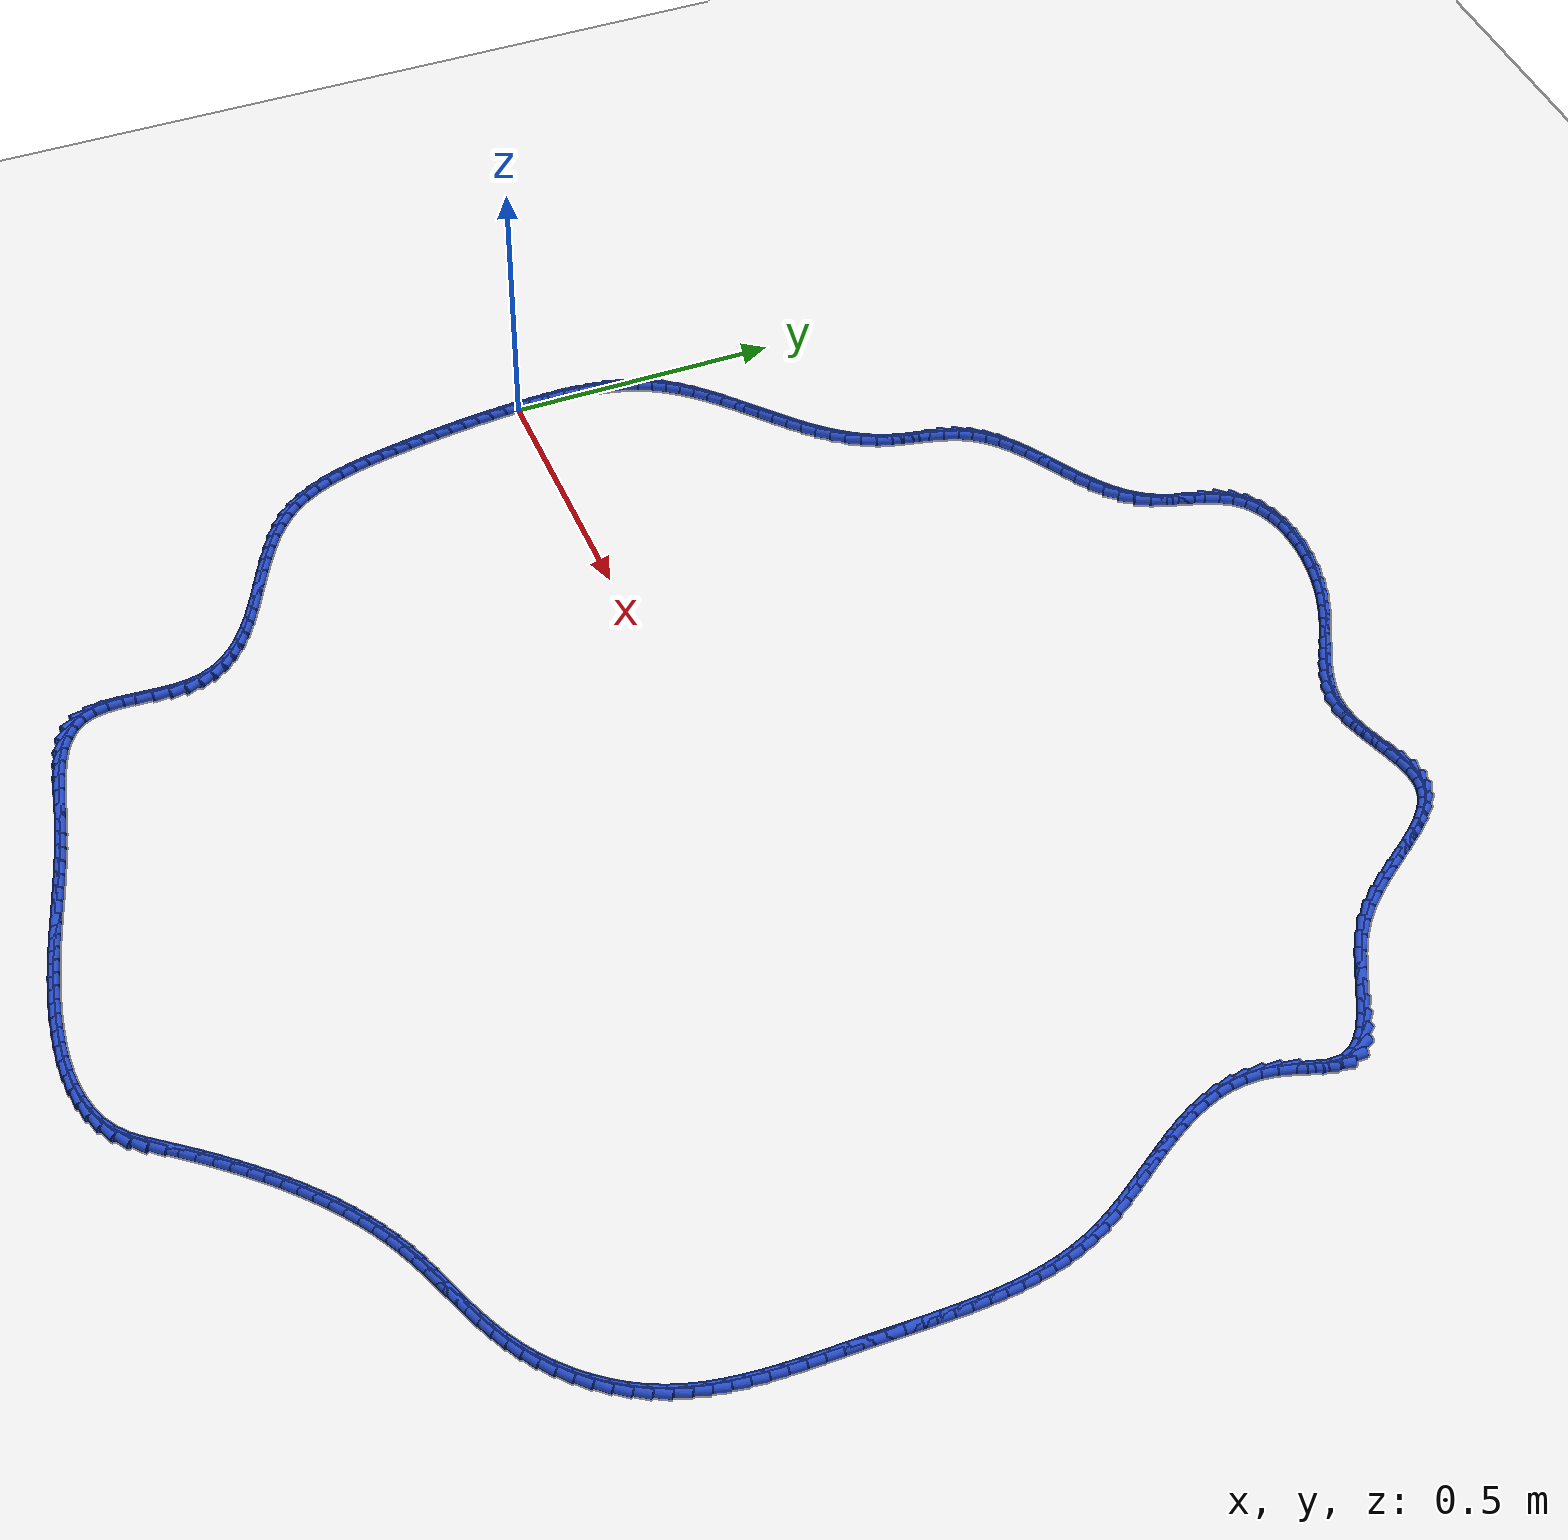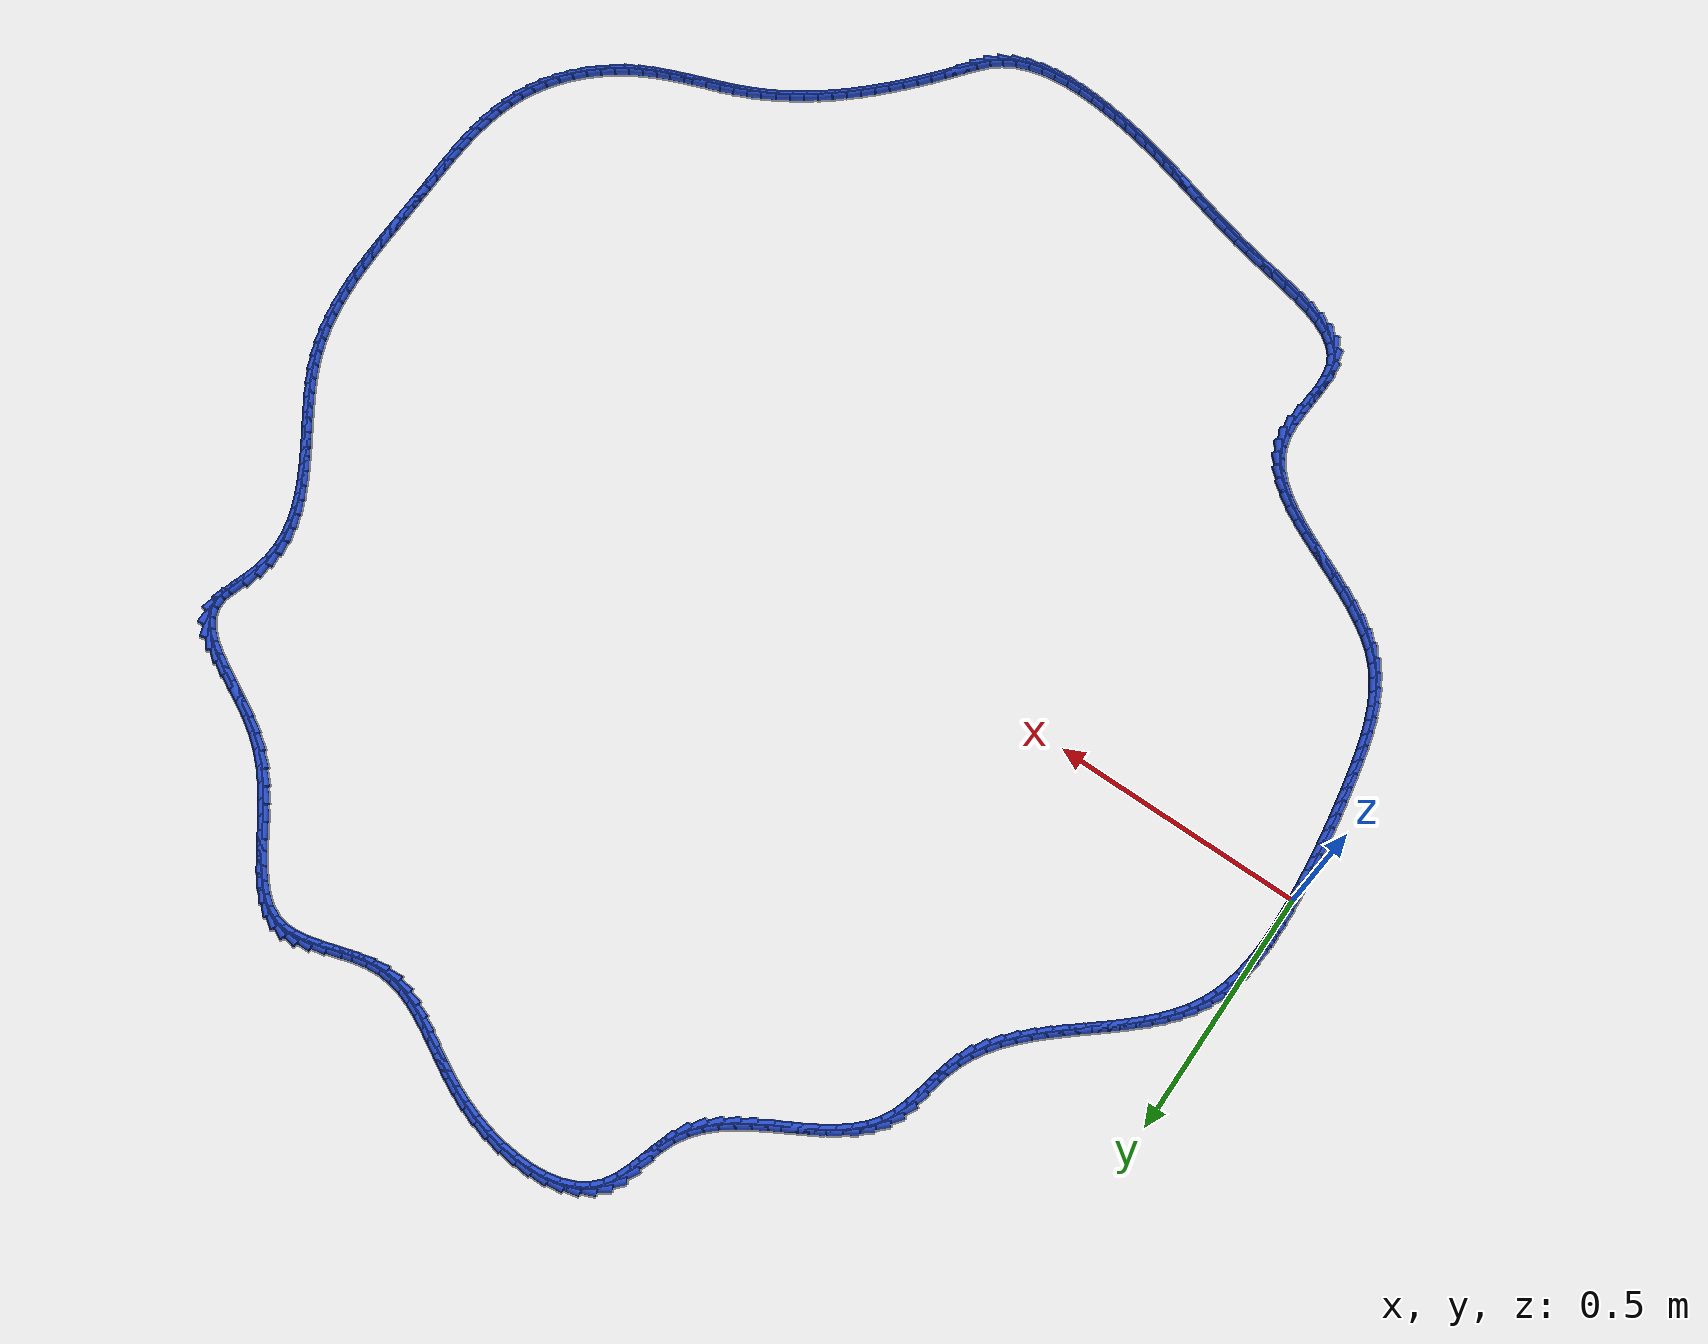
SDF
<sdf version="1.6">
 <world name="default">
  <light name="sun" type="directional">
   <pose>0 0 10 0 -0 0</pose>
   <diffuse>0.8 0.8 0.8 1</diffuse>
   <specular>0.2 0.2 0.2 1</specular>
   <attenuation>
    <range>1000</range>
    <constant>0.9</constant>
    <linear>0.01</linear>
    <quadratic>0.001</quadratic>
   </attenuation>
   <direction>-0.5 0.1 -0.9</direction>
  </light>
  <model name="ground_plane">
   <static>1</static>
   <link name="link">
    <collision name="collision">
     <geometry><plane><normal>0 0 1</normal><size>100 100</size></plane></geometry>
     <surface><friction><ode><mu>100</mu><mu2>50</mu2></ode></friction></surface>
    </collision>
    <visual name="visual">
     <cast_shadows>0</cast_shadows>
     <geometry><plane><normal>0 0 1</normal><size>100 100</size></plane></geometry>
     <material>
      <script><uri>file://media/materials/scripts/gazebo.material</uri><name>Gazebo/WhiteGlow</name></script>
     </material>
    </visual>
   </link>
  </model>
  <gravity>0 0 -9.8</gravity>
  <magnetic_field>6e-06 2.3e-05 -4.2e-05</magnetic_field>
  <atmosphere type="adiabatic"/>
  <physics name="default_physics" default="0" type="ode">
   <max_step_size>0.001</max_step_size>
   <real_time_factor>1</real_time_factor>
   <real_time_update_rate>1000</real_time_update_rate>
  </physics>
  <scene><ambient>0.4 0.4 0.4 1</ambient><background>0.7 0.7 0.7 1</background><shadows>1</shadows></scene>
  <spherical_coordinates>
   <surface_model>EARTH_WGS84</surface_model>
   <latitude_deg>0</latitude_deg>
   <longitude_deg>0</longitude_deg>
   <elevation>0</elevation>
   <heading_deg>0</heading_deg>
  </spherical_coordinates>
  <model name="line">
   <link name="link_0">
    <pose>1.5016200088924236e-17 8.326672684688674e-17 0.01 0 1.57 -1.5213581371606009</pose>
    <collision name="collision">
     <geometry><cylinder><radius>0.01</radius><length>0.08</length></cylinder></geometry>
    </collision>
    <visual name="visual">
     <material>
      <script><name>Gazebo/Blue</name><uri>file://media/materials/scripts/gazebo.material</uri></script>
     </material>
     <geometry><cylinder><radius>0.01</radius><length>0.08</length></cylinder></geometry>
    </visual>
   </link>
   <link name="link_1">
    <pose>-0.001450392091105295 0.029313578391075498 0.01 0 1.57 -1.5459850343110553</pose>
    <collision name="collision">
     <geometry><cylinder><radius>0.01</radius><length>0.08</length></cylinder></geometry>
    </collision>
    <visual name="visual">
     <material>
      <script><name>Gazebo/Blue</name><uri>file://media/materials/scripts/gazebo.material</uri></script>
     </material>
     <geometry><cylinder><radius>0.01</radius><length>0.08</length></cylinder></geometry>
    </visual>
   </link>
   <link name="link_2">
    <pose>-0.0021833481796962335 0.05884874590597099 0.01 0 1.57 1.5627188708161428</pose>
    <collision name="collision">
     <geometry><cylinder><radius>0.01</radius><length>0.08</length></cylinder></geometry>
    </collision>
    <visual name="visual">
     <material>
      <script><name>Gazebo/Blue</name><uri>file://media/materials/scripts/gazebo.material</uri></script>
     </material>
     <geometry><cylinder><radius>0.01</radius><length>0.08</length></cylinder></geometry>
    </visual>
   </link>
   <link name="link_3">
    <pose>-0.0019446907877343292 0.08839421197140855 0.01 0 1.57 1.520932273999409</pose>
    <collision name="collision">
     <geometry><cylinder><radius>0.01</radius><length>0.08</length></cylinder></geometry>
    </collision>
    <visual name="visual">
     <material>
      <script><name>Gazebo/Blue</name><uri>file://media/materials/scripts/gazebo.material</uri></script>
     </material>
     <geometry><cylinder><radius>0.01</radius><length>0.08</length></cylinder></geometry>
    </visual>
   </link>
   <link name="link_4">
    <pose>-0.00048024243718110607 0.1177386860141102 0.01 0 1.57 1.4693759299298257</pose>
    <collision name="collision">
     <geometry><cylinder><radius>0.01</radius><length>0.08</length></cylinder></geometry>
    </collision>
    <visual name="visual">
     <material>
      <script><name>Gazebo/Blue</name><uri>file://media/materials/scripts/gazebo.material</uri></script>
     </material>
     <geometry><cylinder><radius>0.01</radius><length>0.08</length></cylinder></geometry>
    </visual>
   </link>
   <link name="link_5">
    <pose>0.002464174350001914 0.14667087746079793 0.01 0 1.57 1.4070069661162767</pose>
    <collision name="collision">
     <geometry><cylinder><radius>0.01</radius><length>0.08</length></cylinder></geometry>
    </collision>
    <visual name="visual">
     <material>
      <script><name>Gazebo/Blue</name><uri>file://media/materials/scripts/gazebo.material</uri></script>
     </material>
     <geometry><cylinder><radius>0.01</radius><length>0.08</length></cylinder></geometry>
    </visual>
   </link>
   <link name="link_6">
    <pose>0.007142737051853204 0.17497949573819366 0.01 0 1.57 1.3327341369886345</pose>
    <collision name="collision">
     <geometry><cylinder><radius>0.01</radius><length>0.08</length></cylinder></geometry>
    </collision>
    <visual name="visual">
     <material>
      <script><name>Gazebo/Blue</name><uri>file://media/materials/scripts/gazebo.material</uri></script>
     </material>
     <geometry><cylinder><radius>0.01</radius><length>0.08</length></cylinder></geometry>
    </visual>
   </link>
   <link name="link_7">
    <pose>0.013809623146411236 0.2024532502730194 0.01 0 1.57 1.2456377662991511</pose>
    <collision name="collision">
     <geometry><cylinder><radius>0.01</radius><length>0.08</length></cylinder></geometry>
    </collision>
    <visual name="visual">
     <material>
      <script><name>Gazebo/Blue</name><uri>file://media/materials/scripts/gazebo.material</uri></script>
     </material>
     <geometry><cylinder><radius>0.01</radius><length>0.08</length></cylinder></geometry>
    </visual>
   </link>
   <link name="link_8">
    <pose>0.022719010111714493 0.2288808504919972 0.01 0 1.57 1.1453633010345605</pose>
    <collision name="collision">
     <geometry><cylinder><radius>0.01</radius><length>0.08</length></cylinder></geometry>
    </collision>
    <visual name="visual">
     <material>
      <script><name>Gazebo/Blue</name><uri>file://media/materials/scripts/gazebo.material</uri></script>
     </material>
     <geometry><cylinder><radius>0.01</radius><length>0.08</length></cylinder></geometry>
    </visual>
   </link>
   <link name="link_9">
    <pose>0.03412404378283779 0.2540516921947441 0.01 0 1.57 1.0401623220612952</pose>
    <collision name="collision">
     <geometry><cylinder><radius>0.01</radius><length>0.08</length></cylinder></geometry>
    </collision>
    <visual name="visual">
     <material>
      <script><name>Gazebo/Blue</name><uri>file://media/materials/scripts/gazebo.material</uri></script>
     </material>
     <geometry><cylinder><radius>0.01</radius><length>0.08</length></cylinder></geometry>
    </visual>
   </link>
   <link name="link_10">
    <pose>0.04810140152827598 0.2778725792150259 0.01 0 1.57 0.9479354843157908</pose>
    <collision name="collision">
     <geometry><cylinder><radius>0.01</radius><length>0.08</length></cylinder></geometry>
    </collision>
    <visual name="visual">
     <material>
      <script><name>Gazebo/Blue</name><uri>file://media/materials/scripts/gazebo.material</uri></script>
     </material>
     <geometry><cylinder><radius>0.01</radius><length>0.08</length></cylinder></geometry>
    </visual>
   </link>
   <link name="link_11">
    <pose>0.06435299780991255 0.3004996527157634 0.01 0 1.57 0.8716488008830131</pose>
    <collision name="collision">
     <geometry><cylinder><radius>0.01</radius><length>0.08</length></cylinder></geometry>
    </collision>
    <visual name="visual">
     <material>
      <script><name>Gazebo/Blue</name><uri>file://media/materials/scripts/gazebo.material</uri></script>
     </material>
     <geometry><cylinder><radius>0.01</radius><length>0.08</length></cylinder></geometry>
    </visual>
   </link>
   <link name="link_12">
    <pose>0.08253285347012444 0.32212091845202506 0.01 0 1.57 0.81106274656525</pose>
    <collision name="collision">
     <geometry><cylinder><radius>0.01</radius><length>0.08</length></cylinder></geometry>
    </collision>
    <visual name="visual">
     <material>
      <script><name>Gazebo/Blue</name><uri>file://media/materials/scripts/gazebo.material</uri></script>
     </material>
     <geometry><cylinder><radius>0.01</radius><length>0.08</length></cylinder></geometry>
    </visual>
   </link>
   <link name="link_13">
    <pose>0.1022949893512886 0.3429243821788796 0.01 0 1.57 0.7653686024575431</pose>
    <collision name="collision">
     <geometry><cylinder><radius>0.01</radius><length>0.08</length></cylinder></geometry>
    </collision>
    <visual name="visual">
     <material>
      <script><name>Gazebo/Blue</name><uri>file://media/materials/scripts/gazebo.material</uri></script>
     </material>
     <geometry><cylinder><radius>0.01</radius><length>0.08</length></cylinder></geometry>
    </visual>
   </link>
   <link name="link_14">
    <pose>0.12329342629578185 0.3630980496513956 0.01 0 1.57 0.7336220642174771</pose>
    <collision name="collision">
     <geometry><cylinder><radius>0.01</radius><length>0.08</length></cylinder></geometry>
    </collision>
    <visual name="visual">
     <material>
      <script><name>Gazebo/Blue</name><uri>file://media/materials/scripts/gazebo.material</uri></script>
     </material>
     <geometry><cylinder><radius>0.01</radius><length>0.08</length></cylinder></geometry>
    </visual>
   </link>
   <link name="link_15">
    <pose>0.1451821851459812 0.3828299266246413 0.01 0 1.57 0.71500820200426</pose>
    <collision name="collision">
     <geometry><cylinder><radius>0.01</radius><length>0.08</length></cylinder></geometry>
    </collision>
    <visual name="visual">
     <material>
      <script><name>Gazebo/Blue</name><uri>file://media/materials/scripts/gazebo.material</uri></script>
     </material>
     <geometry><cylinder><radius>0.01</radius><length>0.08</length></cylinder></geometry>
    </visual>
   </link>
   <link name="link_16">
    <pose>0.16761528674426357 0.4023080188536857 0.01 0 1.57 0.7089805959570279</pose>
    <collision name="collision">
     <geometry><cylinder><radius>0.01</radius><length>0.08</length></cylinder></geometry>
    </collision>
    <visual name="visual">
     <material>
      <script><name>Gazebo/Blue</name><uri>file://media/materials/scripts/gazebo.material</uri></script>
     </material>
     <geometry><cylinder><radius>0.01</radius><length>0.08</length></cylinder></geometry>
    </visual>
   </link>
   <link name="link_17">
    <pose>0.19024675193300591 0.42172033209359727 0.01 0 1.57 0.7153221707179961</pose>
    <collision name="collision">
     <geometry><cylinder><radius>0.01</radius><length>0.08</length></cylinder></geometry>
    </collision>
    <visual name="visual">
     <material>
      <script><name>Gazebo/Blue</name><uri>file://media/materials/scripts/gazebo.material</uri></script>
     </material>
     <geometry><cylinder><radius>0.01</radius><length>0.08</length></cylinder></geometry>
    </visual>
   </link>
   <link name="link_18">
    <pose>0.21273060155458504 0.4412548720994444 0.01 0 1.57 0.7341586989837482</pose>
    <collision name="collision">
     <geometry><cylinder><radius>0.01</radius><length>0.08</length></cylinder></geometry>
    </collision>
    <visual name="visual">
     <material>
      <script><name>Gazebo/Blue</name><uri>file://media/materials/scripts/gazebo.material</uri></script>
     </material>
     <geometry><cylinder><radius>0.01</radius><length>0.08</length></cylinder></geometry>
    </visual>
   </link>
   <link name="link_19">
    <pose>0.2347208564513779 0.4610996446262959 0.01 0 1.57 0.7659357295823375</pose>
    <collision name="collision">
     <geometry><cylinder><radius>0.01</radius><length>0.08</length></cylinder></geometry>
    </collision>
    <visual name="visual">
     <material>
      <script><name>Gazebo/Blue</name><uri>file://media/materials/scripts/gazebo.material</uri></script>
     </material>
     <geometry><cylinder><radius>0.01</radius><length>0.08</length></cylinder></geometry>
    </visual>
   </link>
   <link name="link_20">
    <pose>0.2558715374657615 0.48144265542922016 0.01 0 1.57 0.8113502055215448</pose>
    <collision name="collision">
     <geometry><cylinder><radius>0.01</radius><length>0.08</length></cylinder></geometry>
    </collision>
    <visual name="visual">
     <material>
      <script><name>Gazebo/Blue</name><uri>file://media/materials/scripts/gazebo.material</uri></script>
     </material>
     <geometry><cylinder><radius>0.01</radius><length>0.08</length></cylinder></geometry>
    </visual>
   </link>
   <link name="link_21">
    <pose>0.2758366654401127 0.5024719102632857 0.01 0 1.57 0.8712096768741262</pose>
    <collision name="collision">
     <geometry><cylinder><radius>0.01</radius><length>0.08</length></cylinder></geometry>
    </collision>
    <visual name="visual">
     <material>
      <script><name>Gazebo/Blue</name><uri>file://media/materials/scripts/gazebo.material</uri></script>
     </material>
     <geometry><cylinder><radius>0.01</radius><length>0.08</length></cylinder></geometry>
    </visual>
   </link>
   <link name="link_22">
    <pose>0.2942702612168084 0.5243754148835613 0.01 0 1.57 0.9461788514459866</pose>
    <collision name="collision">
     <geometry><cylinder><radius>0.01</radius><length>0.08</length></cylinder></geometry>
    </collision>
    <visual name="visual">
     <material>
      <script><name>Gazebo/Blue</name><uri>file://media/materials/scripts/gazebo.material</uri></script>
     </material>
     <geometry><cylinder><radius>0.01</radius><length>0.08</length></cylinder></geometry>
    </visual>
   </link>
   <link name="link_23">
    <pose>0.31082634563822564 0.5473411750451156 0.01 0 1.57 1.0363805787732143</pose>
    <collision name="collision">
     <geometry><cylinder><radius>0.01</radius><length>0.08</length></cylinder></geometry>
    </collision>
    <visual name="visual">
     <material>
      <script><name>Gazebo/Blue</name><uri>file://media/materials/scripts/gazebo.material</uri></script>
     </material>
     <geometry><cylinder><radius>0.01</radius><length>0.08</length></cylinder></geometry>
    </visual>
   </link>
   <link name="link_24">
    <pose>0.32515893954674135 0.571557196503017 0.01 0 1.57 1.1408759366571928</pose>
    <collision name="collision">
     <geometry><cylinder><radius>0.01</radius><length>0.08</length></cylinder></geometry>
    </collision>
    <visual name="visual">
     <material>
      <script><name>Gazebo/Blue</name><uri>file://media/materials/scripts/gazebo.material</uri></script>
     </material>
     <geometry><cylinder><radius>0.01</radius><length>0.08</length></cylinder></geometry>
    </visual>
   </link>
   <link name="link_25">
    <pose>0.3369220637847323 0.597211485012334 0.01 0 1.57 1.2533117832307805</pose>
    <collision name="collision">
     <geometry><cylinder><radius>0.01</radius><length>0.08</length></cylinder></geometry>
    </collision>
    <visual name="visual">
     <material>
      <script><name>Gazebo/Blue</name><uri>file://media/materials/scripts/gazebo.material</uri></script>
     </material>
     <geometry><cylinder><radius>0.01</radius><length>0.08</length></cylinder></geometry>
    </visual>
   </link>
   <link name="link_26">
    <pose>0.3458670698331932 0.6244330474358372 0.01 0 1.57 1.3317815715527865</pose>
    <collision name="collision">
     <geometry><cylinder><radius>0.01</radius><length>0.08</length></cylinder></geometry>
    </collision>
    <visual name="visual">
     <material>
      <script><name>Gazebo/Blue</name><uri>file://media/materials/scripts/gazebo.material</uri></script>
     </material>
     <geometry><cylinder><radius>0.01</radius><length>0.08</length></cylinder></geometry>
    </visual>
   </link>
   <link name="link_27">
    <pose>0.35276320812461914 0.6527338710475734 0.01 0 1.57 1.3559966836559978</pose>
    <collision name="collision">
     <geometry><cylinder><radius>0.01</radius><length>0.08</length></cylinder></geometry>
    </collision>
    <visual name="visual">
     <material>
      <script><name>Gazebo/Blue</name><uri>file://media/materials/scripts/gazebo.material</uri></script>
     </material>
     <geometry><cylinder><radius>0.01</radius><length>0.08</length></cylinder></geometry>
    </visual>
   </link>
   <link name="link_28">
    <pose>0.35898624692629233 0.6812582903359948 0.01 0 1.57 1.327103264247171</pose>
    <collision name="collision">
     <geometry><cylinder><radius>0.01</radius><length>0.08</length></cylinder></geometry>
    </collision>
    <visual name="visual">
     <material>
      <script><name>Gazebo/Blue</name><uri>file://media/materials/scripts/gazebo.material</uri></script>
     </material>
     <geometry><cylinder><radius>0.01</radius><length>0.08</length></cylinder></geometry>
    </visual>
   </link>
   <link name="link_29">
    <pose>0.36592002986289934 0.709145744751891 0.01 0 1.57 1.24116387648521</pose>
    <collision name="collision">
     <geometry><cylinder><radius>0.01</radius><length>0.08</length></cylinder></geometry>
    </collision>
    <visual name="visual">
     <material>
      <script><name>Gazebo/Blue</name><uri>file://media/materials/scripts/gazebo.material</uri></script>
     </material>
     <geometry><cylinder><radius>0.01</radius><length>0.08</length></cylinder></geometry>
    </visual>
   </link>
   <link name="link_30">
    <pose>0.3749484005591267 0.7355356737460504 0.01 0 1.57 1.0928867184606963</pose>
    <collision name="collision">
     <geometry><cylinder><radius>0.01</radius><length>0.08</length></cylinder></geometry>
    </collision>
    <visual name="visual">
     <material>
      <script><name>Gazebo/Blue</name><uri>file://media/materials/scripts/gazebo.material</uri></script>
     </material>
     <geometry><cylinder><radius>0.01</radius><length>0.08</length></cylinder></geometry>
    </visual>
   </link>
   <link name="link_31">
    <pose>0.3874107402021028 0.7595962526437878 0.01 0 1.57 0.9238161267379169</pose>
    <collision name="collision">
     <geometry><cylinder><radius>0.01</radius><length>0.08</length></cylinder></geometry>
    </collision>
    <visual name="visual">
     <material>
      <script><name>Gazebo/Blue</name><uri>file://media/materials/scripts/gazebo.material</uri></script>
     </material>
     <geometry><cylinder><radius>0.01</radius><length>0.08</length></cylinder></geometry>
    </visual>
   </link>
   <link name="link_32">
    <pose>0.4036739899737528 0.7811241403963048 0.01 0 1.57 0.7832656963590083</pose>
    <collision name="collision">
     <geometry><cylinder><radius>0.01</radius><length>0.08</length></cylinder></geometry>
    </collision>
    <visual name="visual">
     <material>
      <script><name>Gazebo/Blue</name><uri>file://media/materials/scripts/gazebo.material</uri></script>
     </material>
     <geometry><cylinder><radius>0.01</radius><length>0.08</length></cylinder></geometry>
    </visual>
   </link>
   <link name="link_33">
    <pose>0.4231597463419113 0.8005269680152354 0.01 0 1.57 0.6757883208692756</pose>
    <collision name="collision">
     <geometry><cylinder><radius>0.01</radius><length>0.08</length></cylinder></geometry>
    </collision>
    <visual name="visual">
     <material>
      <script><name>Gazebo/Blue</name><uri>file://media/materials/scripts/gazebo.material</uri></script>
     </material>
     <geometry><cylinder><radius>0.01</radius><length>0.08</length></cylinder></geometry>
    </visual>
   </link>
   <link name="link_34">
    <pose>0.44525056375168076 0.8182375991968811 0.01 0 1.57 0.5993874406189754</pose>
    <collision name="collision">
     <geometry><cylinder><radius>0.01</radius><length>0.08</length></cylinder></geometry>
    </collision>
    <visual name="visual">
     <material>
      <script><name>Gazebo/Blue</name><uri>file://media/materials/scripts/gazebo.material</uri></script>
     </material>
     <geometry><cylinder><radius>0.01</radius><length>0.08</length></cylinder></geometry>
    </visual>
   </link>
   <link name="link_35">
    <pose>0.46932899664816297 0.834688897637542 0.01 0 1.57 0.5506325841919487</pose>
    <collision name="collision">
     <geometry><cylinder><radius>0.01</radius><length>0.08</length></cylinder></geometry>
    </collision>
    <visual name="visual">
     <material>
      <script><name>Gazebo/Blue</name><uri>file://media/materials/scripts/gazebo.material</uri></script>
     </material>
     <geometry><cylinder><radius>0.01</radius><length>0.08</length></cylinder></geometry>
    </visual>
   </link>
   <link name="link_36">
    <pose>0.4947775994764606 0.8503137270335204 0.01 0 1.57 0.5265672052131826</pose>
    <collision name="collision">
     <geometry><cylinder><radius>0.01</radius><length>0.08</length></cylinder></geometry>
    </collision>
    <visual name="visual">
     <material>
      <script><name>Gazebo/Blue</name><uri>file://media/materials/scripts/gazebo.material</uri></script>
     </material>
     <geometry><cylinder><radius>0.01</radius><length>0.08</length></cylinder></geometry>
    </visual>
   </link>
   <link name="link_37">
    <pose>0.5209789266816753 0.8655449510811162 0.01 0 1.57 0.5254488509580636</pose>
    <collision name="collision">
     <geometry><cylinder><radius>0.01</radius><length>0.08</length></cylinder></geometry>
    </collision>
    <visual name="visual">
     <material>
      <script><name>Gazebo/Blue</name><uri>file://media/materials/scripts/gazebo.material</uri></script>
     </material>
     <geometry><cylinder><radius>0.01</radius><length>0.08</length></cylinder></geometry>
    </visual>
   </link>
   <link name="link_38">
    <pose>0.5473155327089098 0.8808154334766313 0.01 0 1.57 0.5469333132520303</pose>
    <collision name="collision">
     <geometry><cylinder><radius>0.01</radius><length>0.08</length></cylinder></geometry>
    </collision>
    <visual name="visual">
     <material>
      <script><name>Gazebo/Blue</name><uri>file://media/materials/scripts/gazebo.material</uri></script>
     </material>
     <geometry><cylinder><radius>0.01</radius><length>0.08</length></cylinder></geometry>
    </visual>
   </link>
   <link name="link_39">
    <pose>0.573169972003266 0.8965580379163665 0.01 0 1.57 0.5920293379302604</pose>
    <collision name="collision">
     <geometry><cylinder><radius>0.01</radius><length>0.08</length></cylinder></geometry>
    </collision>
    <visual name="visual">
     <material>
      <script><name>Gazebo/Blue</name><uri>file://media/materials/scripts/gazebo.material</uri></script>
     </material>
     <geometry><cylinder><radius>0.01</radius><length>0.08</length></cylinder></geometry>
    </visual>
   </link>
   <link name="link_40">
    <pose>0.5979247990098461 0.9132056280966228 0.01 0 1.57 0.6628574029519354</pose>
    <collision name="collision">
     <geometry><cylinder><radius>0.01</radius><length>0.08</length></cylinder></geometry>
    </collision>
    <visual name="visual">
     <material>
      <script><name>Gazebo/Blue</name><uri>file://media/materials/scripts/gazebo.material</uri></script>
     </material>
     <geometry><cylinder><radius>0.01</radius><length>0.08</length></cylinder></geometry>
    </visual>
   </link>
   <link name="link_41">
    <pose>0.6209625681737522 0.9311910677137014 0.01 0 1.57 0.7619934752384302</pose>
    <collision name="collision">
     <geometry><cylinder><radius>0.01</radius><length>0.08</length></cylinder></geometry>
    </collision>
    <visual name="visual">
     <material>
      <script><name>Gazebo/Blue</name><uri>file://media/materials/scripts/gazebo.material</uri></script>
     </material>
     <geometry><cylinder><radius>0.01</radius><length>0.08</length></cylinder></geometry>
    </visual>
   </link>
   <link name="link_42">
    <pose>0.6416658339400866 0.9509472204639033 0.01 0 1.57 0.8909799531553018</pose>
    <collision name="collision">
     <geometry><cylinder><radius>0.01</radius><length>0.08</length></cylinder></geometry>
    </collision>
    <visual name="visual">
     <material>
      <script><name>Gazebo/Blue</name><uri>file://media/materials/scripts/gazebo.material</uri></script>
     </material>
     <geometry><cylinder><radius>0.01</radius><length>0.08</length></cylinder></geometry>
    </visual>
   </link>
   <link name="link_43">
    <pose>0.6594171507539515 0.9729069500435298 0.01 0 1.57 1.0475604432657277</pose>
    <collision name="collision">
     <geometry><cylinder><radius>0.01</radius><length>0.08</length></cylinder></geometry>
    </collision>
    <visual name="visual">
     <material>
      <script><name>Gazebo/Blue</name><uri>file://media/materials/scripts/gazebo.material</uri></script>
     </material>
     <geometry><cylinder><radius>0.01</radius><length>0.08</length></cylinder></geometry>
    </visual>
   </link>
   <link name="link_44">
    <pose>0.6736037022128786 0.9974993836551991 0.01 0 1.57 1.194021732020882</pose>
    <collision name="collision">
     <geometry><cylinder><radius>0.01</radius><length>0.08</length></cylinder></geometry>
    </collision>
    <visual name="visual">
     <material>
      <script><name>Gazebo/Blue</name><uri>file://media/materials/scripts/gazebo.material</uri></script>
     </material>
     <geometry><cylinder><radius>0.01</radius><length>0.08</length></cylinder></geometry>
    </visual>
   </link>
   <link name="link_45">
    <pose>0.6843199770834671 1.0245827359347883 0.01 0 1.57 1.2688042066182017</pose>
    <collision name="collision">
     <geometry><cylinder><radius>0.01</radius><length>0.08</length></cylinder></geometry>
    </collision>
    <visual name="visual">
     <material>
      <script><name>Gazebo/Blue</name><uri>file://media/materials/scripts/gazebo.material</uri></script>
     </material>
     <geometry><cylinder><radius>0.01</radius><length>0.08</length></cylinder></geometry>
    </visual>
   </link>
   <link name="link_46">
    <pose>0.6931214358187368 1.052835975088329 0.01 0 1.57 1.2716145312156795</pose>
    <collision name="collision">
     <geometry><cylinder><radius>0.01</radius><length>0.08</length></cylinder></geometry>
    </collision>
    <visual name="visual">
     <material>
      <script><name>Gazebo/Blue</name><uri>file://media/materials/scripts/gazebo.material</uri></script>
     </material>
     <geometry><cylinder><radius>0.01</radius><length>0.08</length></cylinder></geometry>
    </visual>
   </link>
   <link name="link_47">
    <pose>0.701744253942763 1.080792202290792 0.01 0 1.57 1.2000890362745547</pose>
    <collision name="collision">
     <geometry><cylinder><radius>0.01</radius><length>0.08</length></cylinder></geometry>
    </collision>
    <visual name="visual">
     <material>
      <script><name>Gazebo/Blue</name><uri>file://media/materials/scripts/gazebo.material</uri></script>
     </material>
     <geometry><cylinder><radius>0.01</radius><length>0.08</length></cylinder></geometry>
    </visual>
   </link>
   <link name="link_48">
    <pose>0.7119246069796211 1.1069845187171479 0.01 0 1.57 1.040197676958847</pose>
    <collision name="collision">
     <geometry><cylinder><radius>0.01</radius><length>0.08</length></cylinder></geometry>
    </collision>
    <visual name="visual">
     <material>
      <script><name>Gazebo/Blue</name><uri>file://media/materials/scripts/gazebo.material</uri></script>
     </material>
     <geometry><cylinder><radius>0.01</radius><length>0.08</length></cylinder></geometry>
    </visual>
   </link>
   <link name="link_49">
    <pose>0.7253972303397928 1.1299470729590937 0.01 0 1.57 0.8073341549045417</pose>
    <collision name="collision">
     <geometry><cylinder><radius>0.01</radius><length>0.08</length></cylinder></geometry>
    </collision>
    <visual name="visual">
     <material>
      <script><name>Gazebo/Blue</name><uri>file://media/materials/scripts/gazebo.material</uri></script>
     </material>
     <geometry><cylinder><radius>0.01</radius><length>0.08</length></cylinder></geometry>
    </visual>
   </link>
   <link name="link_50">
    <pose>0.7432972343025063 1.1486501301714647 0.01 0 1.57 0.5847191276660734</pose>
    <collision name="collision">
     <geometry><cylinder><radius>0.01</radius><length>0.08</length></cylinder></geometry>
    </collision>
    <visual name="visual">
     <material>
      <script><name>Gazebo/Blue</name><uri>file://media/materials/scripts/gazebo.material</uri></script>
     </material>
     <geometry><cylinder><radius>0.01</radius><length>0.08</length></cylinder></geometry>
    </visual>
   </link>
   <link name="link_51">
    <pose>0.7652360269123551 1.1631721675355524 0.01 0 1.57 0.3958051857030596</pose>
    <collision name="collision">
     <geometry><cylinder><radius>0.01</radius><length>0.08</length></cylinder></geometry>
    </collision>
    <visual name="visual">
     <material>
      <script><name>Gazebo/Blue</name><uri>file://media/materials/scripts/gazebo.material</uri></script>
     </material>
     <geometry><cylinder><radius>0.01</radius><length>0.08</length></cylinder></geometry>
    </visual>
   </link>
   <link name="link_52">
    <pose>0.7905865796690845 1.1737650807920883 0.01 0 1.57 0.2410229043029383</pose>
    <collision name="collision">
     <geometry><cylinder><radius>0.01</radius><length>0.08</length></cylinder></geometry>
    </collision>
    <visual name="visual">
     <material>
      <script><name>Gazebo/Blue</name><uri>file://media/materials/scripts/gazebo.material</uri></script>
     </material>
     <geometry><cylinder><radius>0.01</radius><length>0.08</length></cylinder></geometry>
    </visual>
   </link>
   <link name="link_53">
    <pose>0.8187218640724383 1.1806807656818028 0.01 0 1.57 0.11471396210622445</pose>
    <collision name="collision">
     <geometry><cylinder><radius>0.01</radius><length>0.08</length></cylinder></geometry>
    </collision>
    <visual name="visual">
     <material>
      <script><name>Gazebo/Blue</name><uri>file://media/materials/scripts/gazebo.material</uri></script>
     </material>
     <geometry><cylinder><radius>0.01</radius><length>0.08</length></cylinder></geometry>
    </visual>
   </link>
   <link name="link_54">
    <pose>0.849014851622162 1.1841711179454284 0.01 0 1.57 0.00995815317012087</pose>
    <collision name="collision">
     <geometry><cylinder><radius>0.01</radius><length>0.08</length></cylinder></geometry>
    </collision>
    <visual name="visual">
     <material>
      <script><name>Gazebo/Blue</name><uri>file://media/materials/scripts/gazebo.material</uri></script>
     </material>
     <geometry><cylinder><radius>0.01</radius><length>0.08</length></cylinder></geometry>
    </visual>
   </link>
   <link name="link_55">
    <pose>0.880838513818 1.1844880333236962 0.01 0 1.57 -0.07941830753010753</pose>
    <collision name="collision">
     <geometry><cylinder><radius>0.01</radius><length>0.08</length></cylinder></geometry>
    </collision>
    <visual name="visual">
     <material>
      <script><name>Gazebo/Blue</name><uri>file://media/materials/scripts/gazebo.material</uri></script>
     </material>
     <geometry><cylinder><radius>0.01</radius><length>0.08</length></cylinder></geometry>
    </visual>
   </link>
   <link name="link_56">
    <pose>0.9135658221596977 1.1818834075573386 0.01 0 1.57 -0.15846745128347794</pose>
    <collision name="collision">
     <geometry><cylinder><radius>0.01</radius><length>0.08</length></cylinder></geometry>
    </collision>
    <visual name="visual">
     <material>
      <script><name>Gazebo/Blue</name><uri>file://media/materials/scripts/gazebo.material</uri></script>
     </material>
     <geometry><cylinder><radius>0.01</radius><length>0.08</length></cylinder></geometry>
    </visual>
   </link>
   <link name="link_57">
    <pose>0.9465697481469995 1.1766091363870856 0.01 0 1.57 -0.23134719445083093</pose>
    <collision name="collision">
     <geometry><cylinder><radius>0.01</radius><length>0.08</length></cylinder></geometry>
    </collision>
    <visual name="visual">
     <material>
      <script><name>Gazebo/Blue</name><uri>file://media/materials/scripts/gazebo.material</uri></script>
     </material>
     <geometry><cylinder><radius>0.01</radius><length>0.08</length></cylinder></geometry>
    </visual>
   </link>
   <link name="link_58">
    <pose>0.9792232632796497 1.1689171155536697 0.01 0 1.57 -0.30170814702455545</pose>
    <collision name="collision">
     <geometry><cylinder><radius>0.01</radius><length>0.08</length></cylinder></geometry>
    </collision>
    <visual name="visual">
     <material>
      <script><name>Gazebo/Blue</name><uri>file://media/materials/scripts/gazebo.material</uri></script>
     </material>
     <geometry><cylinder><radius>0.01</radius><length>0.08</length></cylinder></geometry>
    </visual>
   </link>
   <link name="link_59">
    <pose>1.0108993390573935 1.1590592407978217 0.01 0 1.57 -0.37099792617253613</pose>
    <collision name="collision">
     <geometry><cylinder><radius>0.01</radius><length>0.08</length></cylinder></geometry>
    </collision>
    <visual name="visual">
     <material>
      <script><name>Gazebo/Blue</name><uri>file://media/materials/scripts/gazebo.material</uri></script>
     </material>
     <geometry><cylinder><radius>0.01</radius><length>0.08</length></cylinder></geometry>
    </visual>
   </link>
   <link name="link_60">
    <pose>1.0410628099872403 1.1473252989424036 0.01 0 1.57 -0.4276714451687227</pose>
    <collision name="collision">
     <geometry><cylinder><radius>0.01</radius><length>0.08</length></cylinder></geometry>
    </collision>
    <visual name="visual">
     <material>
      <script><name>Gazebo/Blue</name><uri>file://media/materials/scripts/gazebo.material</uri></script>
     </material>
     <geometry><cylinder><radius>0.01</radius><length>0.08</length></cylinder></geometry>
    </visual>
   </link>
   <link name="link_61">
    <pose>1.0697600348688074 1.13424494033519 0.01 0 1.57 -0.4651426393354473</pose>
    <collision name="collision">
     <geometry><cylinder><radius>0.01</radius><length>0.08</length></cylinder></geometry>
    </collision>
    <visual name="visual">
     <material>
      <script><name>Gazebo/Blue</name><uri>file://media/materials/scripts/gazebo.material</uri></script>
     </material>
     <geometry><cylinder><radius>0.01</radius><length>0.08</length></cylinder></geometry>
    </visual>
   </link>
   <link name="link_62">
    <pose>1.0972642482409847 1.1204413956184176 0.01 0 1.57 -0.48185883364186716</pose>
    <collision name="collision">
     <geometry><cylinder><radius>0.01</radius><length>0.08</length></cylinder></geometry>
    </collision>
    <visual name="visual">
     <material>
      <script><name>Gazebo/Blue</name><uri>file://media/materials/scripts/gazebo.material</uri></script>
     </material>
     <geometry><cylinder><radius>0.01</radius><length>0.08</length></cylinder></geometry>
    </visual>
   </link>
   <link name="link_63">
    <pose>1.1238492018678674 1.1065381087761605 0.01 0 1.57 -0.4762081415095008</pose>
    <collision name="collision">
     <geometry><cylinder><radius>0.01</radius><length>0.08</length></cylinder></geometry>
    </collision>
    <visual name="visual">
     <material>
      <script><name>Gazebo/Blue</name><uri>file://media/materials/scripts/gazebo.material</uri></script>
     </material>
     <geometry><cylinder><radius>0.01</radius><length>0.08</length></cylinder></geometry>
    </visual>
   </link>
   <link name="link_64">
    <pose>1.1497886475135508 1.093158523792494 0.01 0 1.57 -0.4462460341428907</pose>
    <collision name="collision">
     <geometry><cylinder><radius>0.01</radius><length>0.08</length></cylinder></geometry>
    </collision>
    <visual name="visual">
     <material>
      <script><name>Gazebo/Blue</name><uri>file://media/materials/scripts/gazebo.material</uri></script>
     </material>
     <geometry><cylinder><radius>0.01</radius><length>0.08</length></cylinder></geometry>
    </visual>
   </link>
   <link name="link_65">
    <pose>1.17535633694213 1.080926084651491 0.01 0 1.57 -0.3897450499874253</pose>
    <collision name="collision">
     <geometry><cylinder><radius>0.01</radius><length>0.08</length></cylinder></geometry>
    </collision>
    <visual name="visual">
     <material>
      <script><name>Gazebo/Blue</name><uri>file://media/materials/scripts/gazebo.material</uri></script>
     </material>
     <geometry><cylinder><radius>0.01</radius><length>0.08</length></cylinder></geometry>
    </visual>
   </link>
   <link name="link_66">
    <pose>1.2008260219176996 1.0704642353372267 0.01 0 1.57 -0.3047884634918579</pose>
    <collision name="collision">
     <geometry><cylinder><radius>0.01</radius><length>0.08</length></cylinder></geometry>
    </collision>
    <visual name="visual">
     <material>
      <script><name>Gazebo/Blue</name><uri>file://media/materials/scripts/gazebo.material</uri></script>
     </material>
     <geometry><cylinder><radius>0.01</radius><length>0.08</length></cylinder></geometry>
    </visual>
   </link>
   <link name="link_67">
    <pose>1.226471454204355 1.0623964198337745 0.01 0 1.57 -0.19117359363224684</pose>
    <collision name="collision">
     <geometry><cylinder><radius>0.01</radius><length>0.08</length></cylinder></geometry>
    </collision>
    <visual name="visual">
     <material>
      <script><name>Gazebo/Blue</name><uri>file://media/materials/scripts/gazebo.material</uri></script>
     </material>
     <geometry><cylinder><radius>0.01</radius><length>0.08</length></cylinder></geometry>
    </visual>
   </link>
   <link name="link_68">
    <pose>1.2525663855661913 1.0573460821252094 0.01 0 1.57 -0.05250618684125274</pose>
    <collision name="collision">
     <geometry><cylinder><radius>0.01</radius><length>0.08</length></cylinder></geometry>
    </collision>
    <visual name="visual">
     <material>
      <script><name>Gazebo/Blue</name><uri>file://media/materials/scripts/gazebo.material</uri></script>
     </material>
     <geometry><cylinder><radius>0.01</radius><length>0.08</length></cylinder></geometry>
    </visual>
   </link>
   <link name="link_69">
    <pose>1.2793845677673032 1.055936666195605 0.01 0 1.57 0.10031410568517572</pose>
    <collision name="collision">
     <geometry><cylinder><radius>0.01</radius><length>0.08</length></cylinder></geometry>
    </collision>
    <visual name="visual">
     <material>
      <script><name>Gazebo/Blue</name><uri>file://media/materials/scripts/gazebo.material</uri></script>
     </material>
     <geometry><cylinder><radius>0.01</radius><length>0.08</length></cylinder></geometry>
    </visual>
   </link>
   <link name="link_70">
    <pose>1.3071793977540873 1.0587342700308249 0.01 0 1.57 0.22166899677190446</pose>
    <collision name="collision">
     <geometry><cylinder><radius>0.01</radius><length>0.08</length></cylinder></geometry>
    </collision>
    <visual name="visual">
     <material>
      <script><name>Gazebo/Blue</name><uri>file://media/materials/scripts/gazebo.material</uri></script>
     </material>
     <geometry><cylinder><radius>0.01</radius><length>0.08</length></cylinder></geometry>
    </visual>
   </link>
   <link name="link_71">
    <pose>1.3358071530221405 1.0651861797633229 0.01 0 1.57 0.2866664481189809</pose>
    <collision name="collision">
     <geometry><cylinder><radius>0.01</radius><length>0.08</length></cylinder></geometry>
    </collision>
    <visual name="visual">
     <material>
      <script><name>Gazebo/Blue</name><uri>file://media/materials/scripts/gazebo.material</uri></script>
     </material>
     <geometry><cylinder><radius>0.01</radius><length>0.08</length></cylinder></geometry>
    </visual>
   </link>
   <link name="link_72">
    <pose>1.3647628575318913 1.0737219153687512 0.01 0 1.57 0.3036060930274469</pose>
    <collision name="collision">
     <geometry><cylinder><radius>0.01</radius><length>0.08</length></cylinder></geometry>
    </collision>
    <visual name="visual">
     <material>
      <script><name>Gazebo/Blue</name><uri>file://media/materials/scripts/gazebo.material</uri></script>
     </material>
     <geometry><cylinder><radius>0.01</radius><length>0.08</length></cylinder></geometry>
    </visual>
   </link>
   <link name="link_73">
    <pose>1.3935283737630222 1.0827339167436134 0.01 0 1.57 0.2738246522989612</pose>
    <collision name="collision">
     <geometry><cylinder><radius>0.01</radius><length>0.08</length></cylinder></geometry>
    </collision>
    <visual name="visual">
     <material>
      <script><name>Gazebo/Blue</name><uri>file://media/materials/scripts/gazebo.material</uri></script>
     </material>
     <geometry><cylinder><radius>0.01</radius><length>0.08</length></cylinder></geometry>
    </visual>
   </link>
   <link name="link_74">
    <pose>1.4215855641952166 1.0906146237844156 0.01 0 1.57 0.18934476163672995</pose>
    <collision name="collision">
     <geometry><cylinder><radius>0.01</radius><length>0.08</length></cylinder></geometry>
    </collision>
    <visual name="visual">
     <material>
      <script><name>Gazebo/Blue</name><uri>file://media/materials/scripts/gazebo.material</uri></script>
     </material>
     <geometry><cylinder><radius>0.01</radius><length>0.08</length></cylinder></geometry>
    </visual>
   </link>
   <link name="link_75">
    <pose>1.4484162913081575 1.0957564763876617 0.01 0 1.57 0.03176712716537184</pose>
    <collision name="collision">
     <geometry><cylinder><radius>0.01</radius><length>0.08</length></cylinder></geometry>
    </collision>
    <visual name="visual">
     <material>
      <script><name>Gazebo/Blue</name><uri>file://media/materials/scripts/gazebo.material</uri></script>
     </material>
     <geometry><cylinder><radius>0.01</radius><length>0.08</length></cylinder></geometry>
    </visual>
   </link>
   <link name="link_76">
    <pose>1.4735031208162366 1.096553681075332 0.01 0 1.57 -0.19524741962398884</pose>
    <collision name="collision">
     <geometry><cylinder><radius>0.01</radius><length>0.08</length></cylinder></geometry>
    </collision>
    <visual name="visual">
     <material>
      <script><name>Gazebo/Blue</name><uri>file://media/materials/scripts/gazebo.material</uri></script>
     </material>
     <geometry><cylinder><radius>0.01</radius><length>0.08</length></cylinder></geometry>
    </visual>
   </link>
   <link name="link_77">
    <pose>1.4965644599482912 1.0919929117527956 0.01 0 1.57 -0.41830416688461675</pose>
    <collision name="collision">
     <geometry><cylinder><radius>0.01</radius><length>0.08</length></cylinder></geometry>
    </collision>
    <visual name="visual">
     <material>
      <script><name>Gazebo/Blue</name><uri>file://media/materials/scripts/gazebo.material</uri></script>
     </material>
     <geometry><cylinder><radius>0.01</radius><length>0.08</length></cylinder></geometry>
    </visual>
   </link>
   <link name="link_78">
    <pose>1.5178957043495744 1.0825103191833079 0.01 0 1.57 -0.6027049485236178</pose>
    <collision name="collision">
     <geometry><cylinder><radius>0.01</radius><length>0.08</length></cylinder></geometry>
    </collision>
    <visual name="visual">
     <material>
      <script><name>Gazebo/Blue</name><uri>file://media/materials/scripts/gazebo.material</uri></script>
     </material>
     <geometry><cylinder><radius>0.01</radius><length>0.08</length></cylinder></geometry>
    </visual>
   </link>
   <link name="link_79">
    <pose>1.537878852255092 1.0687596121366774 0.01 0 1.57 -0.7400241955304039</pose>
    <collision name="collision">
     <geometry><cylinder><radius>0.01</radius><length>0.08</length></cylinder></geometry>
    </collision>
    <visual name="visual">
     <material>
      <script><name>Gazebo/Blue</name><uri>file://media/materials/scripts/gazebo.material</uri></script>
     </material>
     <geometry><cylinder><radius>0.01</radius><length>0.08</length></cylinder></geometry>
    </visual>
   </link>
   <link name="link_80">
    <pose>1.5568959018998496 1.0513944993827125 0.01 0 1.57 -0.8341963551185708</pose>
    <collision name="collision">
     <geometry><cylinder><radius>0.01</radius><length>0.08</length></cylinder></geometry>
    </collision>
    <visual name="visual">
     <material>
      <script><name>Gazebo/Blue</name><uri>file://media/materials/scripts/gazebo.material</uri></script>
     </material>
     <geometry><cylinder><radius>0.01</radius><length>0.08</length></cylinder></geometry>
    </visual>
   </link>
   <link name="link_81">
    <pose>1.5753288515188526 1.0310686896912211 0.01 0 1.57 -0.89270725116071</pose>
    <collision name="collision">
     <geometry><cylinder><radius>0.01</radius><length>0.08</length></cylinder></geometry>
    </collision>
    <visual name="visual">
     <material>
      <script><name>Gazebo/Blue</name><uri>file://media/materials/scripts/gazebo.material</uri></script>
     </material>
     <geometry><cylinder><radius>0.01</radius><length>0.08</length></cylinder></geometry>
    </visual>
   </link>
   <link name="link_82">
    <pose>1.5935596993471068 1.0084358918320127 0.01 0 1.57 -0.9221452233148755</pose>
    <collision name="collision">
     <geometry><cylinder><radius>0.01</radius><length>0.08</length></cylinder></geometry>
    </collision>
    <visual name="visual">
     <material>
      <script><name>Gazebo/Blue</name><uri>file://media/materials/scripts/gazebo.material</uri></script>
     </material>
     <geometry><cylinder><radius>0.01</radius><length>0.08</length></cylinder></geometry>
    </visual>
   </link>
   <link name="link_83">
    <pose>1.6119704436196178 0.9841498145748949 0.01 0 1.57 -0.9270825643079603</pose>
    <collision name="collision">
     <geometry><cylinder><radius>0.01</radius><length>0.08</length></cylinder></geometry>
    </collision>
    <visual name="visual">
     <material>
      <script><name>Gazebo/Blue</name><uri>file://media/materials/scripts/gazebo.material</uri></script>
     </material>
     <geometry><cylinder><radius>0.01</radius><length>0.08</length></cylinder></geometry>
    </visual>
   </link>
   <link name="link_84">
    <pose>1.630943082571391 0.9588641666896764 0.01 0 1.57 -0.9102173074113217</pose>
    <collision name="collision">
     <geometry><cylinder><radius>0.01</radius><length>0.08</length></cylinder></geometry>
    </collision>
    <visual name="visual">
     <material>
      <script><name>Gazebo/Blue</name><uri>file://media/materials/scripts/gazebo.material</uri></script>
     </material>
     <geometry><cylinder><radius>0.01</radius><length>0.08</length></cylinder></geometry>
    </visual>
   </link>
   <link name="link_85">
    <pose>1.6508596144374326 0.9332326569461659 0.01 0 1.57 -0.872818818554714</pose>
    <collision name="collision">
     <geometry><cylinder><radius>0.01</radius><length>0.08</length></cylinder></geometry>
    </collision>
    <visual name="visual">
     <material>
      <script><name>Gazebo/Blue</name><uri>file://media/materials/scripts/gazebo.material</uri></script>
     </material>
     <geometry><cylinder><radius>0.01</radius><length>0.08</length></cylinder></geometry>
    </visual>
   </link>
   <link name="link_86">
    <pose>1.672102037452747 0.9079089941141711 0.01 0 1.57 -0.8152291456246085</pose>
    <collision name="collision">
     <geometry><cylinder><radius>0.01</radius><length>0.08</length></cylinder></geometry>
    </collision>
    <visual name="visual">
     <material>
      <script><name>Gazebo/Blue</name><uri>file://media/materials/scripts/gazebo.material</uri></script>
     </material>
     <geometry><cylinder><radius>0.01</radius><length>0.08</length></cylinder></geometry>
    </visual>
   </link>
   <link name="link_87">
    <pose>1.6950523498523413 0.8835468869635017 0.01 0 1.57 -0.7374437605789547</pose>
    <collision name="collision">
     <geometry><cylinder><radius>0.01</radius><length>0.08</length></cylinder></geometry>
    </collision>
    <visual name="visual">
     <material>
      <script><name>Gazebo/Blue</name><uri>file://media/materials/scripts/gazebo.material</uri></script>
     </material>
     <geometry><cylinder><radius>0.01</radius><length>0.08</length></cylinder></geometry>
    </visual>
   </link>
   <link name="link_88">
    <pose>1.7200925498712198 0.8608000442639651 0.01 0 1.57 -0.6406871802630099</pose>
    <collision name="collision">
     <geometry><cylinder><radius>0.01</radius><length>0.08</length></cylinder></geometry>
    </collision>
    <visual name="visual">
     <material>
      <script><name>Gazebo/Blue</name><uri>file://media/materials/scripts/gazebo.material</uri></script>
     </material>
     <geometry><cylinder><radius>0.01</radius><length>0.08</length></cylinder></geometry>
    </visual>
   </link>
   <link name="link_89">
    <pose>1.7475825030954937 0.8403031919359382 0.01 0 1.57 -0.5498484005011435</pose>
    <collision name="collision">
     <geometry><cylinder><radius>0.01</radius><length>0.08</length></cylinder></geometry>
    </collision>
    <visual name="visual">
     <material>
      <script><name>Gazebo/Blue</name><uri>file://media/materials/scripts/gazebo.material</uri></script>
     </material>
     <geometry><cylinder><radius>0.01</radius><length>0.08</length></cylinder></geometry>
    </visual>
   </link>
   <link name="link_90">
    <pose>1.7772303807172538 0.8221321071442437 0.01 0 1.57 -0.489826246227489</pose>
    <collision name="collision">
     <geometry><cylinder><radius>0.01</radius><length>0.08</length></cylinder></geometry>
    </collision>
    <visual name="visual">
     <material>
      <script><name>Gazebo/Blue</name><uri>file://media/materials/scripts/gazebo.material</uri></script>
     </material>
     <geometry><cylinder><radius>0.01</radius><length>0.08</length></cylinder></geometry>
    </visual>
   </link>
   <link name="link_91">
    <pose>1.8080019255286102 0.8057257970675474 0.01 0 1.57 -0.45914361027234185</pose>
    <collision name="collision">
     <geometry><cylinder><radius>0.01</radius><length>0.08</length></cylinder></geometry>
    </collision>
    <visual name="visual">
     <material>
      <script><name>Gazebo/Blue</name><uri>file://media/materials/scripts/gazebo.material</uri></script>
     </material>
     <geometry><cylinder><radius>0.01</radius><length>0.08</length></cylinder></geometry>
    </visual>
   </link>
   <link name="link_92">
    <pose>1.838822504159499 0.7904886388404215 0.01 0 1.57 -0.4573487293777927</pose>
    <collision name="collision">
     <geometry><cylinder><radius>0.01</radius><length>0.08</length></cylinder></geometry>
    </collision>
    <visual name="visual">
     <material>
      <script><name>Gazebo/Blue</name><uri>file://media/materials/scripts/gazebo.material</uri></script>
     </material>
     <geometry><cylinder><radius>0.01</radius><length>0.08</length></cylinder></geometry>
    </visual>
   </link>
   <link name="link_93">
    <pose>1.868617483239857 0.7758250095974385 0.01 0 1.57 -0.48757019294206594</pose>
    <collision name="collision">
     <geometry><cylinder><radius>0.01</radius><length>0.08</length></cylinder></geometry>
    </collision>
    <visual name="visual">
     <material>
      <script><name>Gazebo/Blue</name><uri>file://media/materials/scripts/gazebo.material</uri></script>
     </material>
     <geometry><cylinder><radius>0.01</radius><length>0.08</length></cylinder></geometry>
    </visual>
   </link>
   <link name="link_94">
    <pose>1.8963122293996224 0.7611392864731705 0.01 0 1.57 -0.5579689694212654</pose>
    <collision name="collision">
     <geometry><cylinder><radius>0.01</radius><length>0.08</length></cylinder></geometry>
    </collision>
    <visual name="visual">
     <material>
      <script><name>Gazebo/Blue</name><uri>file://media/materials/scripts/gazebo.material</uri></script>
     </material>
     <geometry><cylinder><radius>0.01</radius><length>0.08</length></cylinder></geometry>
    </visual>
   </link>
   <link name="link_95">
    <pose>1.92083210926873 0.7458358466021895 0.01 0 1.57 -0.6837144523140394</pose>
    <collision name="collision">
     <geometry><cylinder><radius>0.01</radius><length>0.08</length></cylinder></geometry>
    </collision>
    <visual name="visual">
     <material>
      <script><name>Gazebo/Blue</name><uri>file://media/materials/scripts/gazebo.material</uri></script>
     </material>
     <geometry><cylinder><radius>0.01</radius><length>0.08</length></cylinder></geometry>
    </visual>
   </link>
   <link name="link_96">
    <pose>1.9411024894771183 0.7293190671190678 0.01 0 1.57 -0.8866227790710869</pose>
    <collision name="collision">
     <geometry><cylinder><radius>0.01</radius><length>0.08</length></cylinder></geometry>
    </collision>
    <visual name="visual">
     <material>
      <script><name>Gazebo/Blue</name><uri>file://media/materials/scripts/gazebo.material</uri></script>
     </material>
     <geometry><cylinder><radius>0.01</radius><length>0.08</length></cylinder></geometry>
    </visual>
   </link>
   <link name="link_97">
    <pose>1.9560487366547232 0.7109933251583774 0.01 0 1.57 -1.1797165528526883</pose>
    <collision name="collision">
     <geometry><cylinder><radius>0.01</radius><length>0.08</length></cylinder></geometry>
    </collision>
    <visual name="visual">
     <material>
      <script><name>Gazebo/Blue</name><uri>file://media/materials/scripts/gazebo.material</uri></script>
     </material>
     <geometry><cylinder><radius>0.01</radius><length>0.08</length></cylinder></geometry>
    </visual>
   </link>
   <link name="link_98">
    <pose>1.9645962174314813 0.6902629978546908 0.01 0 1.57 -1.5248601027865283</pose>
    <collision name="collision">
     <geometry><cylinder><radius>0.01</radius><length>0.08</length></cylinder></geometry>
    </collision>
    <visual name="visual">
     <material>
      <script><name>Gazebo/Blue</name><uri>file://media/materials/scripts/gazebo.material</uri></script>
     </material>
     <geometry><cylinder><radius>0.01</radius><length>0.08</length></cylinder></geometry>
    </visual>
   </link>
   <link name="link_99">
    <pose>1.9656867942096352 0.6665385928766716 0.01 0 1.57 1.3592866164144677</pose>
    <collision name="collision">
     <geometry><cylinder><radius>0.01</radius><length>0.08</length></cylinder></geometry>
    </collision>
    <visual name="visual">
     <material>
      <script><name>Gazebo/Blue</name><uri>file://media/materials/scripts/gazebo.material</uri></script>
     </material>
     <geometry><cylinder><radius>0.01</radius><length>0.08</length></cylinder></geometry>
    </visual>
   </link>
   <link name="link_100">
    <pose>1.959958549360458 0.6398610057375193 0.01 0 1.57 1.2716642886108653</pose>
    <collision name="collision">
     <geometry><cylinder><radius>0.01</radius><length>0.08</length></cylinder></geometry>
    </collision>
    <visual name="visual">
     <material>
      <script><name>Gazebo/Blue</name><uri>file://media/materials/scripts/gazebo.material</uri></script>
     </material>
     <geometry><cylinder><radius>0.01</radius><length>0.08</length></cylinder></geometry>
    </visual>
   </link>
   <link name="link_101">
    <pose>1.9511938225875047 0.6114396723747569 0.01 0 1.57 1.3104079022236583</pose>
    <collision name="collision">
     <geometry><cylinder><radius>0.01</radius><length>0.08</length></cylinder></geometry>
    </collision>
    <visual name="visual">
     <material>
      <script><name>Gazebo/Blue</name><uri>file://media/materials/scripts/gazebo.material</uri></script>
     </material>
     <geometry><cylinder><radius>0.01</radius><length>0.08</length></cylinder></geometry>
    </visual>
   </link>
   <link name="link_102">
    <pose>1.94351243120654 0.5826096786088142 0.01 0 1.57 1.4415644303944506</pose>
    <collision name="collision">
     <geometry><cylinder><radius>0.01</radius><length>0.08</length></cylinder></geometry>
    </collision>
    <visual name="visual">
     <material>
      <script><name>Gazebo/Blue</name><uri>file://media/materials/scripts/gazebo.material</uri></script>
     </material>
     <geometry><cylinder><radius>0.01</radius><length>0.08</length></cylinder></geometry>
    </visual>
   </link>
   <link name="link_103">
    <pose>1.9398380834825428 0.5543359314568718 0.01 0 1.57 -1.5582476464024653</pose>
    <collision name="collision">
     <geometry><cylinder><radius>0.01</radius><length>0.08</length></cylinder></geometry>
    </collision>
    <visual name="visual">
     <material>
      <script><name>Gazebo/Blue</name><uri>file://media/materials/scripts/gazebo.material</uri></script>
     </material>
     <geometry><cylinder><radius>0.01</radius><length>0.08</length></cylinder></geometry>
    </visual>
   </link>
   <link name="link_104">
    <pose>1.940185110414232 0.526682926895899 0.01 0 1.57 -1.426111541294023</pose>
    <collision name="collision">
     <geometry><cylinder><radius>0.01</radius><length>0.08</length></cylinder></geometry>
    </collision>
    <visual name="visual">
     <material>
      <script><name>Gazebo/Blue</name><uri>file://media/materials/scripts/gazebo.material</uri></script>
     </material>
     <geometry><cylinder><radius>0.01</radius><length>0.08</length></cylinder></geometry>
    </visual>
   </link>
   <link name="link_105">
    <pose>1.9441339575045418 0.49958087948975377 0.01 0 1.57 -1.3090645618036647</pose>
    <collision name="collision">
     <geometry><cylinder><radius>0.01</radius><length>0.08</length></cylinder></geometry>
    </collision>
    <visual name="visual">
     <material>
      <script><name>Gazebo/Blue</name><uri>file://media/materials/scripts/gazebo.material</uri></script>
     </material>
     <geometry><cylinder><radius>0.01</radius><length>0.08</length></cylinder></geometry>
    </visual>
   </link>
   <link name="link_106">
    <pose>1.9512650702564083 0.47296000380229264 0.01 0 1.57 -1.2098443063075954</pose>
    <collision name="collision">
     <geometry><cylinder><radius>0.01</radius><length>0.08</length></cylinder></geometry>
    </collision>
    <visual name="visual">
     <material>
      <script><name>Gazebo/Blue</name><uri>file://media/materials/scripts/gazebo.material</uri></script>
     </material>
     <geometry><cylinder><radius>0.01</radius><length>0.08</length></cylinder></geometry>
    </visual>
   </link>
   <link name="link_107">
    <pose>1.961158894172768 0.44675051439737357 0.01 0 1.57 -1.128934660780634</pose>
    <collision name="collision">
     <geometry><cylinder><radius>0.01</radius><length>0.08</length></cylinder></geometry>
    </collision>
    <visual name="visual">
     <material>
      <script><name>Gazebo/Blue</name><uri>file://media/materials/scripts/gazebo.material</uri></script>
     </material>
     <geometry><cylinder><radius>0.01</radius><length>0.08</length></cylinder></geometry>
    </visual>
   </link>
   <link name="link_108">
    <pose>1.9733958747565559 0.42088262583885383 0.01 0 1.57 -1.06547464182261</pose>
    <collision name="collision">
     <geometry><cylinder><radius>0.01</radius><length>0.08</length></cylinder></geometry>
    </collision>
    <visual name="visual">
     <material>
      <script><name>Gazebo/Blue</name><uri>file://media/materials/scripts/gazebo.material</uri></script>
     </material>
     <geometry><cylinder><radius>0.01</radius><length>0.08</length></cylinder></geometry>
    </visual>
   </link>
   <link name="link_109">
    <pose>1.9875564575107079 0.3952865526905908 0.01 0 1.57 -1.0180701814335957</pose>
    <collision name="collision">
     <geometry><cylinder><radius>0.01</radius><length>0.08</length></cylinder></geometry>
    </collision>
    <visual name="visual">
     <material>
      <script><name>Gazebo/Blue</name><uri>file://media/materials/scripts/gazebo.material</uri></script>
     </material>
     <geometry><cylinder><radius>0.01</radius><length>0.08</length></cylinder></geometry>
    </visual>
   </link>
   <link name="link_110">
    <pose>2.00322108793816 0.3698925095164422 0.01 0 1.57 -0.9853213281584219</pose>
    <collision name="collision">
     <geometry><cylinder><radius>0.01</radius><length>0.08</length></cylinder></geometry>
    </collision>
    <visual name="visual">
     <material>
      <script><name>Gazebo/Blue</name><uri>file://media/materials/scripts/gazebo.material</uri></script>
     </material>
     <geometry><cylinder><radius>0.01</radius><length>0.08</length></cylinder></geometry>
    </visual>
   </link>
   <link name="link_111">
    <pose>2.019970211541847 0.34463071088026503 0.01 0 1.57 -0.9661007872257618</pose>
    <collision name="collision">
     <geometry><cylinder><radius>0.01</radius><length>0.08</length></cylinder></geometry>
    </collision>
    <visual name="visual">
     <material>
      <script><name>Gazebo/Blue</name><uri>file://media/materials/scripts/gazebo.material</uri></script>
     </material>
     <geometry><cylinder><radius>0.01</radius><length>0.08</length></cylinder></geometry>
    </visual>
   </link>
   <link name="link_112">
    <pose>2.037384273824706 0.31943137134591704 0.01 0 1.57 -0.9596769359094095</pose>
    <collision name="collision">
     <geometry><cylinder><radius>0.01</radius><length>0.08</length></cylinder></geometry>
    </collision>
    <visual name="visual">
     <material>
      <script><name>Gazebo/Blue</name><uri>file://media/materials/scripts/gazebo.material</uri></script>
     </material>
     <geometry><cylinder><radius>0.01</radius><length>0.08</length></cylinder></geometry>
    </visual>
   </link>
   <link name="link_113">
    <pose>2.0550437202896714 0.29422470547725543 0.01 0 1.57 -0.9657565607343671</pose>
    <collision name="collision">
     <geometry><cylinder><radius>0.01</radius><length>0.08</length></cylinder></geometry>
    </collision>
    <visual name="visual">
     <material>
      <script><name>Gazebo/Blue</name><uri>file://media/materials/scripts/gazebo.material</uri></script>
     </material>
     <geometry><cylinder><radius>0.01</radius><length>0.08</length></cylinder></geometry>
    </visual>
   </link>
   <link name="link_114">
    <pose>2.0725289964396794 0.2689409278381378 0.01 0 1.57 -0.984489796676276</pose>
    <collision name="collision">
     <geometry><cylinder><radius>0.01</radius><length>0.08</length></cylinder></geometry>
    </collision>
    <visual name="visual">
     <material>
      <script><name>Gazebo/Blue</name><uri>file://media/materials/scripts/gazebo.material</uri></script>
     </material>
     <geometry><cylinder><radius>0.01</radius><length>0.08</length></cylinder></geometry>
    </visual>
   </link>
   <link name="link_115">
    <pose>2.0894205477776655 0.24351025299242132 0.01 0 1.57 -1.0164511597164658</pose>
    <collision name="collision">
     <geometry><cylinder><radius>0.01</radius><length>0.08</length></cylinder></geometry>
    </collision>
    <visual name="visual">
     <material>
      <script><name>Gazebo/Blue</name><uri>file://media/materials/scripts/gazebo.material</uri></script>
     </material>
     <geometry><cylinder><radius>0.01</radius><length>0.08</length></cylinder></geometry>
    </visual>
   </link>
   <link name="link_116">
    <pose>2.105298819806567 0.2178628955039638 0.01 0 1.57 -1.0625859740059256</pose>
    <collision name="collision">
     <geometry><cylinder><radius>0.01</radius><length>0.08</length></cylinder></geometry>
    </collision>
    <visual name="visual">
     <material>
      <script><name>Gazebo/Blue</name><uri>file://media/materials/scripts/gazebo.material</uri></script>
     </material>
     <geometry><cylinder><radius>0.01</radius><length>0.08</length></cylinder></geometry>
    </visual>
   </link>
   <link name="link_117">
    <pose>2.119744258029317 0.1919290699366223 0.01 0 1.57 -1.1237365492112361</pose>
    <collision name="collision">
     <geometry><cylinder><radius>0.01</radius><length>0.08</length></cylinder></geometry>
    </collision>
    <visual name="visual">
     <material>
      <script><name>Gazebo/Blue</name><uri>file://media/materials/scripts/gazebo.material</uri></script>
     </material>
     <geometry><cylinder><radius>0.01</radius><length>0.08</length></cylinder></geometry>
    </visual>
   </link>
   <link name="link_118">
    <pose>2.132347828063362 0.16564062832065254 0.01 0 1.57 -1.191617790047895</pose>
    <collision name="collision">
     <geometry><cylinder><radius>0.01</radius><length>0.08</length></cylinder></geometry>
    </collision>
    <visual name="visual">
     <material>
      <script><name>Gazebo/Blue</name><uri>file://media/materials/scripts/gazebo.material</uri></script>
     </material>
     <geometry><cylinder><radius>0.01</radius><length>0.08</length></cylinder></geometry>
    </visual>
   </link>
   <link name="link_119">
    <pose>2.142974212840617 0.13897202706144798 0.01 0 1.57 -1.2558233624092168</pose>
    <collision name="collision">
     <geometry><cylinder><radius>0.01</radius><length>0.08</length></cylinder></geometry>
    </collision>
    <visual name="visual">
     <material>
      <script><name>Gazebo/Blue</name><uri>file://media/materials/scripts/gazebo.material</uri></script>
     </material>
     <geometry><cylinder><radius>0.01</radius><length>0.08</length></cylinder></geometry>
    </visual>
   </link>
   <link name="link_120">
    <pose>2.151780710491881 0.11194326841424575 0.01 0 1.57 -1.314961346540619</pose>
    <collision name="collision">
     <geometry><cylinder><radius>0.01</radius><length>0.08</length></cylinder></geometry>
    </collision>
    <visual name="visual">
     <material>
      <script><name>Gazebo/Blue</name><uri>file://media/materials/scripts/gazebo.material</uri></script>
     </material>
     <geometry><cylinder><radius>0.01</radius><length>0.08</length></cylinder></geometry>
    </visual>
   </link>
   <link name="link_121">
    <pose>2.158938924121176 0.08457658121774304 0.01 0 1.57 -1.3683674331051552</pose>
    <collision name="collision">
     <geometry><cylinder><radius>0.01</radius><length>0.08</length></cylinder></geometry>
    </collision>
    <visual name="visual">
     <material>
      <script><name>Gazebo/Blue</name><uri>file://media/materials/scripts/gazebo.material</uri></script>
     </material>
     <geometry><cylinder><radius>0.01</radius><length>0.08</length></cylinder></geometry>
    </visual>
   </link>
   <link name="link_122">
    <pose>2.164620456832524 0.05689419431063829 0.01 0 1.57 -1.4156171990382425</pose>
    <collision name="collision">
     <geometry><cylinder><radius>0.01</radius><length>0.08</length></cylinder></geometry>
    </collision>
    <visual name="visual">
     <material>
      <script><name>Gazebo/Blue</name><uri>file://media/materials/scripts/gazebo.material</uri></script>
     </material>
     <geometry><cylinder><radius>0.01</radius><length>0.08</length></cylinder></geometry>
    </visual>
   </link>
   <link name="link_123">
    <pose>2.1689969117299457 0.028918336531629472 0.01 0 1.57 -1.456489247013561</pose>
    <collision name="collision">
     <geometry><cylinder><radius>0.01</radius><length>0.08</length></cylinder></geometry>
    </collision>
    <visual name="visual">
     <material>
      <script><name>Gazebo/Blue</name><uri>file://media/materials/scripts/gazebo.material</uri></script>
     </material>
     <geometry><cylinder><radius>0.01</radius><length>0.08</length></cylinder></geometry>
    </visual>
   </link>
   <link name="link_124">
    <pose>2.1722398919174633 0.0006712367194146203 0.01 0 1.57 -1.4909168428152415</pose>
    <collision name="collision">
     <geometry><cylinder><radius>0.01</radius><length>0.08</length></cylinder></geometry>
    </collision>
    <visual name="visual">
     <material>
      <script><name>Gazebo/Blue</name><uri>file://media/materials/scripts/gazebo.material</uri></script>
     </material>
     <geometry><cylinder><radius>0.01</radius><length>0.08</length></cylinder></geometry>
    </visual>
   </link>
   <link name="link_125">
    <pose>2.174521000499098 -0.027824876287308287 0.01 0 1.57 -1.518938625194315</pose>
    <collision name="collision">
     <geometry><cylinder><radius>0.01</radius><length>0.08</length></cylinder></geometry>
    </collision>
    <visual name="visual">
     <material>
      <script><name>Gazebo/Blue</name><uri>file://media/materials/scripts/gazebo.material</uri></script>
     </material>
     <geometry><cylinder><radius>0.01</radius><length>0.08</length></cylinder></geometry>
    </visual>
   </link>
   <link name="link_126">
    <pose>2.1760118405788718 -0.05654777364984127 0.01 0 1.57 -1.5406550438106408</pose>
    <collision name="collision">
     <geometry><cylinder><radius>0.01</radius><length>0.08</length></cylinder></geometry>
    </collision>
    <visual name="visual">
     <material>
      <script><name>Gazebo/Blue</name><uri>file://media/materials/scripts/gazebo.material</uri></script>
     </material>
     <geometry><cylinder><radius>0.01</radius><length>0.08</length></cylinder></geometry>
    </visual>
   </link>
   <link name="link_127">
    <pose>2.1768840152608058 -0.0854752265294863 0.01 0 1.57 -1.556193599560228</pose>
    <collision name="collision">
     <geometry><cylinder><radius>0.01</radius><length>0.08</length></cylinder></geometry>
    </collision>
    <visual name="visual">
     <material>
      <script><name>Gazebo/Blue</name><uri>file://media/materials/scripts/gazebo.material</uri></script>
     </material>
     <geometry><cylinder><radius>0.01</radius><length>0.08</length></cylinder></geometry>
    </visual>
   </link>
   <link name="link_128">
    <pose>2.177309127648921 -0.11458500608754536 0.01 0 1.57 -1.565683497237959</pose>
    <collision name="collision">
     <geometry><cylinder><radius>0.01</radius><length>0.08</length></cylinder></geometry>
    </collision>
    <visual name="visual">
     <material>
      <script><name>Gazebo/Blue</name><uri>file://media/materials/scripts/gazebo.material</uri></script>
     </material>
     <geometry><cylinder><radius>0.01</radius><length>0.08</length></cylinder></geometry>
    </visual>
   </link>
   <link name="link_129">
    <pose>2.17745878084724 -0.1438548834853205 0.01 0 1.57 -1.5692390134632246</pose>
    <collision name="collision">
     <geometry><cylinder><radius>0.01</radius><length>0.08</length></cylinder></geometry>
    </collision>
    <visual name="visual">
     <material>
      <script><name>Gazebo/Blue</name><uri>file://media/materials/scripts/gazebo.material</uri></script>
     </material>
     <geometry><cylinder><radius>0.01</radius><length>0.08</length></cylinder></geometry>
    </visual>
   </link>
   <link name="link_130">
    <pose>2.177504577959784 -0.1732626298841137 0.01 0 1.57 -1.566950441068009</pose>
    <collision name="collision">
     <geometry><cylinder><radius>0.01</radius><length>0.08</length></cylinder></geometry>
    </collision>
    <visual name="visual">
     <material>
      <script><name>Gazebo/Blue</name><uri>file://media/materials/scripts/gazebo.material</uri></script>
     </material>
     <geometry><cylinder><radius>0.01</radius><length>0.08</length></cylinder></geometry>
    </visual>
   </link>
   <link name="link_131">
    <pose>2.1776181220905735 -0.20278601644522692 0.01 0 1.57 -1.5596740774624422</pose>
    <collision name="collision">
     <geometry><cylinder><radius>0.01</radius><length>0.08</length></cylinder></geometry>
    </collision>
    <visual name="visual">
     <material>
      <script><name>Gazebo/Blue</name><uri>file://media/materials/scripts/gazebo.material</uri></script>
     </material>
     <geometry><cylinder><radius>0.01</radius><length>0.08</length></cylinder></geometry>
    </visual>
   </link>
   <link name="link_132">
    <pose>2.177947505500928 -0.23239961512790597 0.01 0 1.57 -1.5555225324323705</pose>
    <collision name="collision">
     <geometry><cylinder><radius>0.01</radius><length>0.08</length></cylinder></geometry>
    </collision>
    <visual name="visual">
     <material>
      <script><name>Gazebo/Blue</name><uri>file://media/materials/scripts/gazebo.material</uri></script>
     </material>
     <geometry><cylinder><radius>0.01</radius><length>0.08</length></cylinder></geometry>
    </visual>
   </link>
   <link name="link_133">
    <pose>2.1784003424312615 -0.26204527521153936 0.01 0 1.57 -1.5592075502950762</pose>
    <collision name="collision">
     <geometry><cylinder><radius>0.01</radius><length>0.08</length></cylinder></geometry>
    </collision>
    <visual name="visual">
     <material>
      <script><name>Gazebo/Blue</name><uri>file://media/materials/scripts/gazebo.material</uri></script>
     </material>
     <geometry><cylinder><radius>0.01</radius><length>0.08</length></cylinder></geometry>
    </visual>
   </link>
   <link name="link_134">
    <pose>2.1787433902533517 -0.29164567909198613 0.01 0 1.57 1.5707364297577495</pose>
    <collision name="collision">
     <geometry><cylinder><radius>0.01</radius><length>0.08</length></cylinder></geometry>
    </collision>
    <visual name="visual">
     <material>
      <script><name>Gazebo/Blue</name><uri>file://media/materials/scripts/gazebo.material</uri></script>
     </material>
     <geometry><cylinder><radius>0.01</radius><length>0.08</length></cylinder></geometry>
    </visual>
   </link>
   <link name="link_135">
    <pose>2.1787416246331883 -0.32112326672220776 0.01 0 1.57 1.5509335433791798</pose>
    <collision name="collision">
     <geometry><cylinder><radius>0.01</radius><length>0.08</length></cylinder></geometry>
    </collision>
    <visual name="visual">
     <material>
      <script><name>Gazebo/Blue</name><uri>file://media/materials/scripts/gazebo.material</uri></script>
     </material>
     <geometry><cylinder><radius>0.01</radius><length>0.08</length></cylinder></geometry>
    </visual>
   </link>
   <link name="link_136">
    <pose>2.178160021236759 -0.350400478055166 0.01 0 1.57 1.5226783109100777</pose>
    <collision name="collision">
     <geometry><cylinder><radius>0.01</radius><length>0.08</length></cylinder></geometry>
    </collision>
    <visual name="visual">
     <material>
      <script><name>Gazebo/Blue</name><uri>file://media/materials/scripts/gazebo.material</uri></script>
     </material>
     <geometry><cylinder><radius>0.01</radius><length>0.08</length></cylinder></geometry>
    </visual>
   </link>
   <link name="link_137">
    <pose>2.176763555730054 -0.3793997530438225 0.01 0 1.57 1.4855970300248549</pose>
    <collision name="collision">
     <geometry><cylinder><radius>0.01</radius><length>0.08</length></cylinder></geometry>
    </collision>
    <visual name="visual">
     <material>
      <script><name>Gazebo/Blue</name><uri>file://media/materials/scripts/gazebo.material</uri></script>
     </material>
     <geometry><cylinder><radius>0.01</radius><length>0.08</length></cylinder></geometry>
    </visual>
   </link>
   <link name="link_138">
    <pose>2.17431720377906 -0.4080435316411386 0.01 0 1.57 1.4392956042225409</pose>
    <collision name="collision">
     <geometry><cylinder><radius>0.01</radius><length>0.08</length></cylinder></geometry>
    </collision>
    <visual name="visual">
     <material>
      <script><name>Gazebo/Blue</name><uri>file://media/materials/scripts/gazebo.material</uri></script>
     </material>
     <geometry><cylinder><radius>0.01</radius><length>0.08</length></cylinder></geometry>
    </visual>
   </link>
   <link name="link_139">
    <pose>2.170585941049768 -0.4362542538000761 0.01 0 1.57 1.3834463359710636</pose>
    <collision name="collision">
     <geometry><cylinder><radius>0.01</radius><length>0.08</length></cylinder></geometry>
    </collision>
    <visual name="visual">
     <material>
      <script><name>Gazebo/Blue</name><uri>file://media/materials/scripts/gazebo.material</uri></script>
     </material>
     <geometry><cylinder><radius>0.01</radius><length>0.08</length></cylinder></geometry>
    </visual>
   </link>
   <link name="link_140">
    <pose>2.1653347432081644 -0.4639543594735965 0.01 0 1.57 1.3179125066724109</pose>
    <collision name="collision">
     <geometry><cylinder><radius>0.01</radius><length>0.08</length></cylinder></geometry>
    </collision>
    <visual name="visual">
     <material>
      <script><name>Gazebo/Blue</name><uri>file://media/materials/scripts/gazebo.material</uri></script>
     </material>
     <geometry><cylinder><radius>0.01</radius><length>0.08</length></cylinder></geometry>
    </visual>
   </link>
   <link name="link_141">
    <pose>2.15832858592024 -0.49106628861466145 0.01 0 1.57 1.24290748565568</pose>
    <collision name="collision">
     <geometry><cylinder><radius>0.01</radius><length>0.08</length></cylinder></geometry>
    </collision>
    <visual name="visual">
     <material>
      <script><name>Gazebo/Blue</name><uri>file://media/materials/scripts/gazebo.material</uri></script>
     </material>
     <geometry><cylinder><radius>0.01</radius><length>0.08</length></cylinder></geometry>
    </visual>
   </link>
   <link name="link_142">
    <pose>2.1493324448519813 -0.5175124811762325 0.01 0 1.57 1.159165580374533</pose>
    <collision name="collision">
     <geometry><cylinder><radius>0.01</radius><length>0.08</length></cylinder></geometry>
    </collision>
    <visual name="visual">
     <material>
      <script><name>Gazebo/Blue</name><uri>file://media/materials/scripts/gazebo.material</uri></script>
     </material>
     <geometry><cylinder><radius>0.01</radius><length>0.08</length></cylinder></geometry>
    </visual>
   </link>
   <link name="link_143">
    <pose>2.138111296062309 -0.5432153770368457 0.01 0 1.57 1.070256707628655</pose>
    <collision name="collision">
     <geometry><cylinder><radius>0.01</radius><length>0.08</length></cylinder></geometry>
    </collision>
    <visual name="visual">
     <material>
      <script><name>Gazebo/Blue</name><uri>file://media/materials/scripts/gazebo.material</uri></script>
     </material>
     <geometry><cylinder><radius>0.01</radius><length>0.08</length></cylinder></geometry>
    </visual>
   </link>
   <link name="link_144">
    <pose>2.124508899725825 -0.5680824935011975 0.01 0 1.57 0.9851370315072407</pose>
    <collision name="collision">
     <geometry><cylinder><radius>0.01</radius><length>0.08</length></cylinder></geometry>
    </collision>
    <visual name="visual">
     <material>
      <script><name>Gazebo/Blue</name><uri>file://media/materials/scripts/gazebo.material</uri></script>
     </material>
     <geometry><cylinder><radius>0.01</radius><length>0.08</length></cylinder></geometry>
    </visual>
   </link>
   <link name="link_145">
    <pose>2.108668145786676 -0.5919646894215107 0.01 0 1.57 0.9047653772155894</pose>
    <collision name="collision">
     <geometry><cylinder><radius>0.01</radius><length>0.08</length></cylinder></geometry>
    </collision>
    <visual name="visual">
     <material>
      <script><name>Gazebo/Blue</name><uri>file://media/materials/scripts/gazebo.material</uri></script>
     </material>
     <geometry><cylinder><radius>0.01</radius><length>0.08</length></cylinder></geometry>
    </visual>
   </link>
   <link name="link_146">
    <pose>2.0908029062440012 -0.6146993788718632 0.01 0 1.57 0.8279205633235612</pose>
    <collision name="collision">
     <geometry><cylinder><radius>0.01</radius><length>0.08</length></cylinder></geometry>
    </collision>
    <visual name="visual">
     <material>
      <script><name>Gazebo/Blue</name><uri>file://media/materials/scripts/gazebo.material</uri></script>
     </material>
     <geometry><cylinder><radius>0.01</radius><length>0.08</length></cylinder></geometry>
    </visual>
   </link>
   <link name="link_147">
    <pose>2.0711270530969412 -0.6361239759263299 0.01 0 1.57 0.7533729343449498</pose>
    <collision name="collision">
     <geometry><cylinder><radius>0.01</radius><length>0.08</length></cylinder></geometry>
    </collision>
    <visual name="visual">
     <material>
      <script><name>Gazebo/Blue</name><uri>file://media/materials/scripts/gazebo.material</uri></script>
     </material>
     <geometry><cylinder><radius>0.01</radius><length>0.08</length></cylinder></geometry>
    </visual>
   </link>
   <link name="link_148">
    <pose>2.0498544583446345 -0.6560758946589864 0.01 0 1.57 0.6798947225078926</pose>
    <collision name="collision">
     <geometry><cylinder><radius>0.01</radius><length>0.08</length></cylinder></geometry>
    </collision>
    <visual name="visual">
     <material>
      <script><name>Gazebo/Blue</name><uri>file://media/materials/scripts/gazebo.material</uri></script>
     </material>
     <geometry><cylinder><radius>0.01</radius><length>0.08</length></cylinder></geometry>
    </visual>
   </link>
   <link name="link_149">
    <pose>2.0271989939862216 -0.6743925491439088 0.01 0 1.57 0.6062521403244878</pose>
    <collision name="collision">
     <geometry><cylinder><radius>0.01</radius><length>0.08</length></cylinder></geometry>
    </collision>
    <visual name="visual">
     <material>
      <script><name>Gazebo/Blue</name><uri>file://media/materials/scripts/gazebo.material</uri></script>
     </material>
     <geometry><cylinder><radius>0.01</radius><length>0.08</length></cylinder></geometry>
    </visual>
   </link>
   <link name="link_150">
    <pose>2.003374532020841 -0.6909113534551728 0.01 0 1.57 0.532793385031627</pose>
    <collision name="collision">
     <geometry><cylinder><radius>0.01</radius><length>0.08</length></cylinder></geometry>
    </collision>
    <visual name="visual">
     <material>
      <script><name>Gazebo/Blue</name><uri>file://media/materials/scripts/gazebo.material</uri></script>
     </material>
     <geometry><cylinder><radius>0.01</radius><length>0.08</length></cylinder></geometry>
    </visual>
   </link>
   <link name="link_151">
    <pose>1.9785915926286304 -0.7055252462401531 0.01 0 1.57 0.4689941015839314</pose>
    <collision name="collision">
     <geometry><cylinder><radius>0.01</radius><length>0.08</length></cylinder></geometry>
    </collision>
    <visual name="visual">
     <material>
      <script><name>Gazebo/Blue</name><uri>file://media/materials/scripts/gazebo.material</uri></script>
     </material>
     <geometry><cylinder><radius>0.01</radius><length>0.08</length></cylinder></geometry>
    </visual>
   </link>
   <link name="link_152">
    <pose>1.9530398592361438 -0.7184723374846078 0.01 0 1.57 0.4192963553525784</pose>
    <collision name="collision">
     <geometry><cylinder><radius>0.01</radius><length>0.08</length></cylinder></geometry>
    </collision>
    <visual name="visual">
     <material>
      <script><name>Gazebo/Blue</name><uri>file://media/materials/scripts/gazebo.material</uri></script>
     </material>
     <geometry><cylinder><radius>0.01</radius><length>0.08</length></cylinder></geometry>
    </visual>
   </link>
   <link name="link_153">
    <pose>1.9269010206735355 -0.7301231716981672 0.01 0 1.57 0.3839987366928588</pose>
    <collision name="collision">
     <geometry><cylinder><radius>0.01</radius><length>0.08</length></cylinder></geometry>
    </collision>
    <visual name="visual">
     <material>
      <script><name>Gazebo/Blue</name><uri>file://media/materials/scripts/gazebo.material</uri></script>
     </material>
     <geometry><cylinder><radius>0.01</radius><length>0.08</length></cylinder></geometry>
    </visual>
   </link>
   <link name="link_154">
    <pose>1.9003567493396964 -0.7408485655826355 0.01 0 1.57 0.3631116952908933</pose>
    <collision name="collision">
     <geometry><cylinder><radius>0.01</radius><length>0.08</length></cylinder></geometry>
    </collision>
    <visual name="visual">
     <material>
      <script><name>Gazebo/Blue</name><uri>file://media/materials/scripts/gazebo.material</uri></script>
     </material>
     <geometry><cylinder><radius>0.01</radius><length>0.08</length></cylinder></geometry>
    </visual>
   </link>
   <link name="link_155">
    <pose>1.8735887176335169 -0.7510193358398176 0.01 0 1.57 0.3565834362175257</pose>
    <collision name="collision">
     <geometry><cylinder><radius>0.01</radius><length>0.08</length></cylinder></geometry>
    </collision>
    <visual name="visual">
     <material>
      <script><name>Gazebo/Blue</name><uri>file://media/materials/scripts/gazebo.material</uri></script>
     </material>
     <geometry><cylinder><radius>0.01</radius><length>0.08</length></cylinder></geometry>
    </visual>
   </link>
   <link name="link_156">
    <pose>1.8467785979538878 -0.761006299171518 0.01 0 1.57 0.36442972092847686</pose>
    <collision name="collision">
     <geometry><cylinder><radius>0.01</radius><length>0.08</length></cylinder></geometry>
    </collision>
    <visual name="visual">
     <material>
      <script><name>Gazebo/Blue</name><uri>file://media/materials/scripts/gazebo.material</uri></script>
     </material>
     <geometry><cylinder><radius>0.01</radius><length>0.08</length></cylinder></geometry>
    </visual>
   </link>
   <link name="link_157">
    <pose>1.8201080626996997 -0.7711802722795413 0.01 0 1.57 0.3867750837548463</pose>
    <collision name="collision">
     <geometry><cylinder><radius>0.01</radius><length>0.08</length></cylinder></geometry>
    </collision>
    <visual name="visual">
     <material>
      <script><name>Gazebo/Blue</name><uri>file://media/materials/scripts/gazebo.material</uri></script>
     </material>
     <geometry><cylinder><radius>0.01</radius><length>0.08</length></cylinder></geometry>
    </visual>
   </link>
   <link name="link_158">
    <pose>1.7937587842698428 -0.7819120718656923 0.01 0 1.57 0.42380529924486554</pose>
    <collision name="collision">
     <geometry><cylinder><radius>0.01</radius><length>0.08</length></cylinder></geometry>
    </collision>
    <visual name="visual">
     <material>
      <script><name>Gazebo/Blue</name><uri>file://media/materials/scripts/gazebo.material</uri></script>
     </material>
     <geometry><cylinder><radius>0.01</radius><length>0.08</length></cylinder></geometry>
    </visual>
   </link>
   <link name="link_159">
    <pose>1.7679124335396175 -0.7935725112691795 0.01 0 1.57 0.4724409163797906</pose>
    <collision name="collision">
     <geometry><cylinder><radius>0.01</radius><length>0.08</length></cylinder></geometry>
    </collision>
    <visual name="visual">
     <material>
      <script><name>Gazebo/Blue</name><uri>file://media/materials/scripts/gazebo.material</uri></script>
     </material>
     <geometry><cylinder><radius>0.01</radius><length>0.08</length></cylinder></geometry>
    </visual>
   </link>
   <link name="link_160">
    <pose>1.7427134419149362 -0.8064502155371035 0.01 0 1.57 0.5211316696237953</pose>
    <collision name="collision">
     <geometry><cylinder><radius>0.01</radius><length>0.08</length></cylinder></geometry>
    </collision>
    <visual name="visual">
     <material>
      <script><name>Gazebo/Blue</name><uri>file://media/materials/scripts/gazebo.material</uri></script>
     </material>
     <geometry><cylinder><radius>0.01</radius><length>0.08</length></cylinder></geometry>
    </visual>
   </link>
   <link name="link_161">
    <pose>1.7181723856046178 -0.8205383884815307 0.01 0 1.57 0.5671680925409253</pose>
    <collision name="collision">
     <geometry><cylinder><radius>0.01</radius><length>0.08</length></cylinder></geometry>
    </collision>
    <visual name="visual">
     <material>
      <script><name>Gazebo/Blue</name><uri>file://media/materials/scripts/gazebo.material</uri></script>
     </material>
     <geometry><cylinder><radius>0.01</radius><length>0.08</length></cylinder></geometry>
    </visual>
   </link>
   <link name="link_162">
    <pose>1.6942697768142179 -0.8357638820270551 0.01 0 1.57 0.6104697178454417</pose>
    <collision name="collision">
     <geometry><cylinder><radius>0.01</radius><length>0.08</length></cylinder></geometry>
    </collision>
    <visual name="visual">
     <material>
      <script><name>Gazebo/Blue</name><uri>file://media/materials/scripts/gazebo.material</uri></script>
     </material>
     <geometry><cylinder><radius>0.01</radius><length>0.08</length></cylinder></geometry>
    </visual>
   </link>
   <link name="link_163">
    <pose>1.6709861277492888 -0.8520535480982708 0.01 0 1.57 0.6510072088173618</pose>
    <collision name="collision">
     <geometry><cylinder><radius>0.01</radius><length>0.08</length></cylinder></geometry>
    </collision>
    <visual name="visual">
     <material>
      <script><name>Gazebo/Blue</name><uri>file://media/materials/scripts/gazebo.material</uri></script>
     </material>
     <geometry><cylinder><radius>0.01</radius><length>0.08</length></cylinder></geometry>
    </visual>
   </link>
   <link name="link_164">
    <pose>1.6483019506153862 -0.8693342386197724 0.01 0 1.57 0.6887926547073</pose>
    <collision name="collision">
     <geometry><cylinder><radius>0.01</radius><length>0.08</length></cylinder></geometry>
    </collision>
    <visual name="visual">
     <material>
      <script><name>Gazebo/Blue</name><uri>file://media/materials/scripts/gazebo.material</uri></script>
     </material>
     <geometry><cylinder><radius>0.01</radius><length>0.08</length></cylinder></geometry>
    </visual>
   </link>
   <link name="link_165">
    <pose>1.6261977576180622 -0.8875328055161534 0.01 0 1.57 0.7238699428039904</pose>
    <collision name="collision">
     <geometry><cylinder><radius>0.01</radius><length>0.08</length></cylinder></geometry>
    </collision>
    <visual name="visual">
     <material>
      <script><name>Gazebo/Blue</name><uri>file://media/materials/scripts/gazebo.material</uri></script>
     </material>
     <geometry><cylinder><radius>0.01</radius><length>0.08</length></cylinder></geometry>
    </visual>
   </link>
   <link name="link_166">
    <pose>1.604654060962872 -0.9065761007120084 0.01 0 1.57 0.7563058448182598</pose>
    <collision name="collision">
     <geometry><cylinder><radius>0.01</radius><length>0.08</length></cylinder></geometry>
    </collision>
    <visual name="visual">
     <material>
      <script><name>Gazebo/Blue</name><uri>file://media/materials/scripts/gazebo.material</uri></script>
     </material>
     <geometry><cylinder><radius>0.01</radius><length>0.08</length></cylinder></geometry>
    </visual>
   </link>
   <link name="link_167">
    <pose>1.5836513728553694 -0.926390976131932 0.01 0 1.57 0.7861821765553042</pose>
    <collision name="collision">
     <geometry><cylinder><radius>0.01</radius><length>0.08</length></cylinder></geometry>
    </collision>
    <visual name="visual">
     <material>
      <script><name>Gazebo/Blue</name><uri>file://media/materials/scripts/gazebo.material</uri></script>
     </material>
     <geometry><cylinder><radius>0.01</radius><length>0.08</length></cylinder></geometry>
    </visual>
   </link>
   <link name="link_168">
    <pose>1.563170205501108 -0.9469042837005175 0.01 0 1.57 0.8135891697807469</pose>
    <collision name="collision">
     <geometry><cylinder><radius>0.01</radius><length>0.08</length></cylinder></geometry>
    </collision>
    <visual name="visual">
     <material>
      <script><name>Gazebo/Blue</name><uri>file://media/materials/scripts/gazebo.material</uri></script>
     </material>
     <geometry><cylinder><radius>0.01</radius><length>0.08</length></cylinder></geometry>
    </visual>
   </link>
   <link name="link_169">
    <pose>1.5431910711056422 -0.9680428753423598 0.01 0 1.57 0.8386200409446154</pose>
    <collision name="collision">
     <geometry><cylinder><radius>0.01</radius><length>0.08</length></cylinder></geometry>
    </collision>
    <visual name="visual">
     <material>
      <script><name>Gazebo/Blue</name><uri>file://media/materials/scripts/gazebo.material</uri></script>
     </material>
     <geometry><cylinder><radius>0.01</radius><length>0.08</length></cylinder></geometry>
    </visual>
   </link>
   <link name="link_170">
    <pose>1.5236944818745255 -0.9897336029820526 0.01 0 1.57 0.8613666460338486</pose>
    <collision name="collision">
     <geometry><cylinder><radius>0.01</radius><length>0.08</length></cylinder></geometry>
    </collision>
    <visual name="visual">
     <material>
      <script><name>Gazebo/Blue</name><uri>file://media/materials/scripts/gazebo.material</uri></script>
     </material>
     <geometry><cylinder><radius>0.01</radius><length>0.08</length></cylinder></geometry>
    </visual>
   </link>
   <link name="link_171">
    <pose>1.5046609500133123 -1.0119033185441901 0.01 0 1.57 0.8819160611468101</pose>
    <collision name="collision">
     <geometry><cylinder><radius>0.01</radius><length>0.08</length></cylinder></geometry>
    </collision>
    <visual name="visual">
     <material>
      <script><name>Gazebo/Blue</name><uri>file://media/materials/scripts/gazebo.material</uri></script>
     </material>
     <geometry><cylinder><radius>0.01</radius><length>0.08</length></cylinder></geometry>
    </visual>
   </link>
   <link name="link_172">
    <pose>1.486070987727556 -1.034478873953367 0.01 0 1.57 0.9003479104283613</pose>
    <collision name="collision">
     <geometry><cylinder><radius>0.01</radius><length>0.08</length></cylinder></geometry>
    </collision>
    <visual name="visual">
     <material>
      <script><name>Gazebo/Blue</name><uri>file://media/materials/scripts/gazebo.material</uri></script>
     </material>
     <geometry><cylinder><radius>0.01</radius><length>0.08</length></cylinder></geometry>
    </visual>
   </link>
   <link name="link_173">
    <pose>1.4679051072228109 -1.057387121134177 0.01 0 1.57 0.9167322646533754</pose>
    <collision name="collision">
     <geometry><cylinder><radius>0.01</radius><length>0.08</length></cylinder></geometry>
    </collision>
    <visual name="visual">
     <material>
      <script><name>Gazebo/Blue</name><uri>file://media/materials/scripts/gazebo.material</uri></script>
     </material>
     <geometry><cylinder><radius>0.01</radius><length>0.08</length></cylinder></geometry>
    </visual>
   </link>
   <link name="link_174">
    <pose>1.4501438207046309 -1.0805549120112143 0.01 0 1.57 0.9195971540964153</pose>
    <collision name="collision">
     <geometry><cylinder><radius>0.01</radius><length>0.08</length></cylinder></geometry>
    </collision>
    <visual name="visual">
     <material>
      <script><name>Gazebo/Blue</name><uri>file://media/materials/scripts/gazebo.material</uri></script>
     </material>
     <geometry><cylinder><radius>0.01</radius><length>0.08</length></cylinder></geometry>
    </visual>
   </link>
   <link name="link_175">
    <pose>1.4325550790156971 -1.1036342724626091 0.01 0 1.57 0.8533619447222993</pose>
    <collision name="collision">
     <geometry><cylinder><radius>0.01</radius><length>0.08</length></cylinder></geometry>
    </collision>
    <visual name="visual">
     <material>
      <script><name>Gazebo/Blue</name><uri>file://media/materials/scripts/gazebo.material</uri></script>
     </material>
     <geometry><cylinder><radius>0.01</radius><length>0.08</length></cylinder></geometry>
    </visual>
   </link>
   <link name="link_176">
    <pose>1.413916002960035 -1.124996158756465 0.01 0 1.57 0.701745331134811</pose>
    <collision name="collision">
     <geometry><cylinder><radius>0.01</radius><length>0.08</length></cylinder></geometry>
    </collision>
    <visual name="visual">
     <material>
      <script><name>Gazebo/Blue</name><uri>file://media/materials/scripts/gazebo.material</uri></script>
     </material>
     <geometry><cylinder><radius>0.01</radius><length>0.08</length></cylinder></geometry>
    </visual>
   </link>
   <link name="link_177">
    <pose>1.3928490613906435 -1.1428035458487704 0.01 0 1.57 0.529217641748181</pose>
    <collision name="collision">
     <geometry><cylinder><radius>0.01</radius><length>0.08</length></cylinder></geometry>
    </collision>
    <visual name="visual">
     <material>
      <script><name>Gazebo/Blue</name><uri>file://media/materials/scripts/gazebo.material</uri></script>
     </material>
     <geometry><cylinder><radius>0.01</radius><length>0.08</length></cylinder></geometry>
    </visual>
   </link>
   <link name="link_178">
    <pose>1.3691490919572964 -1.1566648652787217 0.01 0 1.57 0.3771596546458779</pose>
    <collision name="collision">
     <geometry><cylinder><radius>0.01</radius><length>0.08</length></cylinder></geometry>
    </collision>
    <visual name="visual">
     <material>
      <script><name>Gazebo/Blue</name><uri>file://media/materials/scripts/gazebo.material</uri></script>
     </material>
     <geometry><cylinder><radius>0.01</radius><length>0.08</length></cylinder></geometry>
    </visual>
   </link>
   <link name="link_179">
    <pose>1.3432178409890947 -1.1669368296249087 0.01 0 1.57 0.248593783584787</pose>
    <collision name="collision">
     <geometry><cylinder><radius>0.01</radius><length>0.08</length></cylinder></geometry>
    </collision>
    <visual name="visual">
     <material>
      <script><name>Gazebo/Blue</name><uri>file://media/materials/scripts/gazebo.material</uri></script>
     </material>
     <geometry><cylinder><radius>0.01</radius><length>0.08</length></cylinder></geometry>
    </visual>
   </link>
   <link name="link_180">
    <pose>1.3154621682874283 -1.1739824560624614 0.01 0 1.57 0.14239085393636816</pose>
    <collision name="collision">
     <geometry><cylinder><radius>0.01</radius><length>0.08</length></cylinder></geometry>
    </collision>
    <visual name="visual">
     <material>
      <script><name>Gazebo/Blue</name><uri>file://media/materials/scripts/gazebo.material</uri></script>
     </material>
     <geometry><cylinder><radius>0.01</radius><length>0.08</length></cylinder></geometry>
    </visual>
   </link>
   <link name="link_181">
    <pose>1.2862889336536876 -1.1781647617665088 0.01 0 1.57 0.055667501691149465</pose>
    <collision name="collision">
     <geometry><cylinder><radius>0.01</radius><length>0.08</length></cylinder></geometry>
    </collision>
    <visual name="visual">
     <material>
      <script><name>Gazebo/Blue</name><uri>file://media/materials/scripts/gazebo.material</uri></script>
     </material>
     <geometry><cylinder><radius>0.01</radius><length>0.08</length></cylinder></geometry>
    </visual>
   </link>
   <link name="link_182">
    <pose>1.2561049968892617 -1.1798467639121804 0.01 0 1.57 -0.014786745526537692</pose>
    <collision name="collision">
     <geometry><cylinder><radius>0.01</radius><length>0.08</length></cylinder></geometry>
    </collision>
    <visual name="visual">
     <material>
      <script><name>Gazebo/Blue</name><uri>file://media/materials/scripts/gazebo.material</uri></script>
     </material>
     <geometry><cylinder><radius>0.01</radius><length>0.08</length></cylinder></geometry>
    </visual>
   </link>
   <link name="link_183">
    <pose>1.2253172177955403 -1.179391479674605 0.01 0 1.57 -0.07183264386928316</pose>
    <collision name="collision">
     <geometry><cylinder><radius>0.01</radius><length>0.08</length></cylinder></geometry>
    </collision>
    <visual name="visual">
     <material>
      <script><name>Gazebo/Blue</name><uri>file://media/materials/scripts/gazebo.material</uri></script>
     </material>
     <geometry><cylinder><radius>0.01</radius><length>0.08</length></cylinder></geometry>
    </visual>
   </link>
   <link name="link_184">
    <pose>1.1943324561739141 -1.1771619262289135 0.01 0 1.57 -0.11775710234143633</pose>
    <collision name="collision">
     <geometry><cylinder><radius>0.01</radius><length>0.08</length></cylinder></geometry>
    </collision>
    <visual name="visual">
     <material>
      <script><name>Gazebo/Blue</name><uri>file://media/materials/scripts/gazebo.material</uri></script>
     </material>
     <geometry><cylinder><radius>0.01</radius><length>0.08</length></cylinder></geometry>
    </visual>
   </link>
   <link name="link_185">
    <pose>1.1635575718257722 -1.1735211207502347 0.01 0 1.57 -0.15424667513396223</pose>
    <collision name="collision">
     <geometry><cylinder><radius>0.01</radius><length>0.08</length></cylinder></geometry>
    </collision>
    <visual name="visual">
     <material>
      <script><name>Gazebo/Blue</name><uri>file://media/materials/scripts/gazebo.material</uri></script>
     </material>
     <geometry><cylinder><radius>0.01</radius><length>0.08</length></cylinder></geometry>
    </visual>
   </link>
   <link name="link_186">
    <pose>1.1333994245525048 -1.1688320804136978 0.01 0 1.57 -0.18316222749459607</pose>
    <collision name="collision">
     <geometry><cylinder><radius>0.01</radius><length>0.08</length></cylinder></geometry>
    </collision>
    <visual name="visual">
     <material>
      <script><name>Gazebo/Blue</name><uri>file://media/materials/scripts/gazebo.material</uri></script>
     </material>
     <geometry><cylinder><radius>0.01</radius><length>0.08</length></cylinder></geometry>
    </visual>
   </link>
   <link name="link_187">
    <pose>1.1041965371031142 -1.1634225854655889 0.01 0 1.57 -0.20886353143769096</pose>
    <collision name="collision">
     <geometry><cylinder><radius>0.01</radius><length>0.08</length></cylinder></geometry>
    </collision>
    <visual name="visual">
     <material>
      <script><name>Gazebo/Blue</name><uri>file://media/materials/scripts/gazebo.material</uri></script>
     </material>
     <geometry><cylinder><radius>0.01</radius><length>0.08</length></cylinder></geometry>
    </visual>
   </link>
   <link name="link_188">
    <pose>1.0759143589069107 -1.15742804674848 0.01 0 1.57 -0.23224584012515598</pose>
    <collision name="collision">
     <geometry><cylinder><radius>0.01</radius><length>0.08</length></cylinder></geometry>
    </collision>
    <visual name="visual">
     <material>
      <script><name>Gazebo/Blue</name><uri>file://media/materials/scripts/gazebo.material</uri></script>
     </material>
     <geometry><cylinder><radius>0.01</radius><length>0.08</length></cylinder></geometry>
    </visual>
   </link>
   <link name="link_189">
    <pose>1.048391659726906 -1.1509185547226415 0.01 0 1.57 -0.2527679408412235</pose>
    <collision name="collision">
     <geometry><cylinder><radius>0.01</radius><length>0.08</length></cylinder></geometry>
    </collision>
    <visual name="visual">
     <material>
      <script><name>Gazebo/Blue</name><uri>file://media/materials/scripts/gazebo.material</uri></script>
     </material>
     <geometry><cylinder><radius>0.01</radius><length>0.08</length></cylinder></geometry>
    </visual>
   </link>
   <link name="link_190">
    <pose>1.0214671057085585 -1.1439641464195778 0.01 0 1.57 -0.2699505281779774</pose>
    <collision name="collision">
     <geometry><cylinder><radius>0.01</radius><length>0.08</length></cylinder></geometry>
    </collision>
    <visual name="visual">
     <material>
      <script><name>Gazebo/Blue</name><uri>file://media/materials/scripts/gazebo.material</uri></script>
     </material>
     <geometry><cylinder><radius>0.01</radius><length>0.08</length></cylinder></geometry>
    </visual>
   </link>
   <link name="link_191">
    <pose>0.9949793629973284 -1.1366348588707953 0.01 0 1.57 -0.2834032967819705</pose>
    <collision name="collision">
     <geometry><cylinder><radius>0.01</radius><length>0.08</length></cylinder></geometry>
    </collision>
    <visual name="visual">
     <material>
      <script><name>Gazebo/Blue</name><uri>file://media/materials/scripts/gazebo.material</uri></script>
     </material>
     <geometry><cylinder><radius>0.01</radius><length>0.08</length></cylinder></geometry>
    </visual>
   </link>
   <link name="link_192">
    <pose>0.9687670977386754 -1.1290007291077997 0.01 0 1.57 -0.2928447103133973</pose>
    <collision name="collision">
     <geometry><cylinder><radius>0.01</radius><length>0.08</length></cylinder></geometry>
    </collision>
    <visual name="visual">
     <material>
      <script><name>Gazebo/Blue</name><uri>file://media/materials/scripts/gazebo.material</uri></script>
     </material>
     <geometry><cylinder><radius>0.01</radius><length>0.08</length></cylinder></geometry>
    </visual>
   </link>
   <link name="link_193">
    <pose>0.9426689760780592 -1.1211317941620964 0.01 0 1.57 -0.2981142589502924</pose>
    <collision name="collision">
     <geometry><cylinder><radius>0.01</radius><length>0.08</length></cylinder></geometry>
    </collision>
    <visual name="visual">
     <material>
      <script><name>Gazebo/Blue</name><uri>file://media/materials/scripts/gazebo.material</uri></script>
     </material>
     <geometry><cylinder><radius>0.01</radius><length>0.08</length></cylinder></geometry>
    </visual>
   </link>
   <link name="link_194">
    <pose>0.9165236641609388 -1.1130980910651909 0.01 0 1.57 -0.29917686131377474</pose>
    <collision name="collision">
     <geometry><cylinder><radius>0.01</radius><length>0.08</length></cylinder></geometry>
    </collision>
    <visual name="visual">
     <material>
      <script><name>Gazebo/Blue</name><uri>file://media/materials/scripts/gazebo.material</uri></script>
     </material>
     <geometry><cylinder><radius>0.01</radius><length>0.08</length></cylinder></geometry>
    </visual>
   </link>
   <link name="link_195">
    <pose>0.8901698281327745 -1.1049696568485887 0.01 0 1.57 -0.2961198330288646</pose>
    <collision name="collision">
     <geometry><cylinder><radius>0.01</radius><length>0.08</length></cylinder></geometry>
    </collision>
    <visual name="visual">
     <material>
      <script><name>Gazebo/Blue</name><uri>file://media/materials/scripts/gazebo.material</uri></script>
     </material>
     <geometry><cylinder><radius>0.01</radius><length>0.08</length></cylinder></geometry>
    </visual>
   </link>
   <link name="link_196">
    <pose>0.8634461341390253 -1.0968165285437952 0.01 0 1.57 -0.2891433324270293</pose>
    <collision name="collision">
     <geometry><cylinder><radius>0.01</radius><length>0.08</length></cylinder></geometry>
    </collision>
    <visual name="visual">
     <material>
      <script><name>Gazebo/Blue</name><uri>file://media/materials/scripts/gazebo.material</uri></script>
     </material>
     <geometry><cylinder><radius>0.01</radius><length>0.08</length></cylinder></geometry>
    </visual>
   </link>
   <link name="link_197">
    <pose>0.8361912483251511 -1.0887087431823166 0.01 0 1.57 -0.2785454559136197</pose>
    <collision name="collision">
     <geometry><cylinder><radius>0.01</radius><length>0.08</length></cylinder></geometry>
    </collision>
    <visual name="visual">
     <material>
      <script><name>Gazebo/Blue</name><uri>file://media/materials/scripts/gazebo.material</uri></script>
     </material>
     <geometry><cylinder><radius>0.01</radius><length>0.08</length></cylinder></geometry>
    </visual>
   </link>
   <link name="link_198">
    <pose>0.8082438368366115 -1.080716337795658 0.01 0 1.57 -0.2647032945214171</pose>
    <collision name="collision">
     <geometry><cylinder><radius>0.01</radius><length>0.08</length></cylinder></geometry>
    </collision>
    <visual name="visual">
     <material>
      <script><name>Gazebo/Blue</name><uri>file://media/materials/scripts/gazebo.material</uri></script>
     </material>
     <geometry><cylinder><radius>0.01</radius><length>0.08</length></cylinder></geometry>
    </visual>
   </link>
   <link name="link_199">
    <pose>0.7794425658188658 -1.0729093494153248 0.01 0 1.57 -0.2480513626688092</pose>
    <collision name="collision">
     <geometry><cylinder><radius>0.01</radius><length>0.08</length></cylinder></geometry>
    </collision>
    <visual name="visual">
     <material>
      <script><name>Gazebo/Blue</name><uri>file://media/materials/scripts/gazebo.material</uri></script>
     </material>
     <geometry><cylinder><radius>0.01</radius><length>0.08</length></cylinder></geometry>
    </visual>
   </link>
   <link name="link_200">
    <pose>0.7496261014173742 -1.0653578150728231 0.01 0 1.57 -0.2291412981669909</pose>
    <collision name="collision">
     <geometry><cylinder><radius>0.01</radius><length>0.08</length></cylinder></geometry>
    </collision>
    <visual name="visual">
     <material>
      <script><name>Gazebo/Blue</name><uri>file://media/materials/scripts/gazebo.material</uri></script>
     </material>
     <geometry><cylinder><radius>0.01</radius><length>0.08</length></cylinder></geometry>
    </visual>
   </link>
   <link name="link_201">
    <pose>0.7186365345360262 -1.0581298777344623 0.01 0 1.57 -0.21603525200630033</pose>
    <collision name="collision">
     <geometry><cylinder><radius>0.01</radius><length>0.08</length></cylinder></geometry>
    </collision>
    <visual name="visual">
     <material>
      <script><name>Gazebo/Blue</name><uri>file://media/materials/scripts/gazebo.material</uri></script>
     </material>
     <geometry><cylinder><radius>0.01</radius><length>0.08</length></cylinder></geometry>
    </visual>
   </link>
   <link name="link_202">
    <pose>0.6866484813266964 -1.0511097770309576 0.01 0 1.57 -0.22180947699744252</pose>
    <collision name="collision">
     <geometry><cylinder><radius>0.01</radius><length>0.08</length></cylinder></geometry>
    </collision>
    <visual name="visual">
     <material>
      <script><name>Gazebo/Blue</name><uri>file://media/materials/scripts/gazebo.material</uri></script>
     </material>
     <geometry><cylinder><radius>0.01</radius><length>0.08</length></cylinder></geometry>
    </visual>
   </link>
   <link name="link_203">
    <pose>0.6544424444067778 -1.0438466666328592 0.01 0 1.57 -0.2478901440350046</pose>
    <collision name="collision">
     <geometry><cylinder><radius>0.01</radius><length>0.08</length></cylinder></geometry>
    </collision>
    <visual name="visual">
     <material>
      <script><name>Gazebo/Blue</name><uri>file://media/materials/scripts/gazebo.material</uri></script>
     </material>
     <geometry><cylinder><radius>0.01</radius><length>0.08</length></cylinder></geometry>
    </visual>
   </link>
   <link name="link_204">
    <pose>0.6228632723341104 -1.0358541136405186 0.01 0 1.57 -0.2968169790559106</pose>
    <collision name="collision">
     <geometry><cylinder><radius>0.01</radius><length>0.08</length></cylinder></geometry>
    </collision>
    <visual name="visual">
     <material>
      <script><name>Gazebo/Blue</name><uri>file://media/materials/scripts/gazebo.material</uri></script>
     </material>
     <geometry><cylinder><radius>0.01</radius><length>0.08</length></cylinder></geometry>
    </visual>
   </link>
   <link name="link_205">
    <pose>0.5927558136665336 -1.0266456851542862 0.01 0 1.57 -0.3741117953949592</pose>
    <collision name="collision">
     <geometry><cylinder><radius>0.01</radius><length>0.08</length></cylinder></geometry>
    </collision>
    <visual name="visual">
     <material>
      <script><name>Gazebo/Blue</name><uri>file://media/materials/scripts/gazebo.material</uri></script>
     </material>
     <geometry><cylinder><radius>0.01</radius><length>0.08</length></cylinder></geometry>
    </visual>
   </link>
   <link name="link_206">
    <pose>0.564964916961888 -1.0157349482745148 0.01 0 1.57 -0.4888108206955174</pose>
    <collision name="collision">
     <geometry><cylinder><radius>0.01</radius><length>0.08</length></cylinder></geometry>
    </collision>
    <visual name="visual">
     <material>
      <script><name>Gazebo/Blue</name><uri>file://media/materials/scripts/gazebo.material</uri></script>
     </material>
     <geometry><cylinder><radius>0.01</radius><length>0.08</length></cylinder></geometry>
    </visual>
   </link>
   <link name="link_207">
    <pose>0.5403354307780129 -1.0026354701015547 0.01 0 1.57 -0.652967455353738</pose>
    <collision name="collision">
     <geometry><cylinder><radius>0.01</radius><length>0.08</length></cylinder></geometry>
    </collision>
    <visual name="visual">
     <material>
      <script><name>Gazebo/Blue</name><uri>file://media/materials/scripts/gazebo.material</uri></script>
     </material>
     <geometry><cylinder><radius>0.01</radius><length>0.08</length></cylinder></geometry>
    </visual>
   </link>
   <link name="link_208">
    <pose>0.5197122036727486 -0.9868608177357575 0.01 0 1.57 -0.8763104453581495</pose>
    <collision name="collision">
     <geometry><cylinder><radius>0.01</radius><length>0.08</length></cylinder></geometry>
    </collision>
    <visual name="visual">
     <material>
      <script><name>Gazebo/Blue</name><uri>file://media/materials/scripts/gazebo.material</uri></script>
     </material>
     <geometry><cylinder><radius>0.01</radius><length>0.08</length></cylinder></geometry>
    </visual>
   </link>
   <link name="link_209">
    <pose>0.5039400842039352 -0.9679245582774753 0.01 0 1.57 -1.1496402097353786</pose>
    <collision name="collision">
     <geometry><cylinder><radius>0.01</radius><length>0.08</length></cylinder></geometry>
    </collision>
    <visual name="visual">
     <material>
      <script><name>Gazebo/Blue</name><uri>file://media/materials/scripts/gazebo.material</uri></script>
     </material>
     <geometry><cylinder><radius>0.01</radius><length>0.08</length></cylinder></geometry>
    </visual>
   </link>
   <link name="link_210">
    <pose>0.49383182659970476 -0.9453594655690976 0.01 0 1.57 -1.3918114968433126</pose>
    <collision name="collision">
     <geometry><cylinder><radius>0.01</radius><length>0.08</length></cylinder></geometry>
    </collision>
    <visual name="visual">
     <material>
      <script><name>Gazebo/Blue</name><uri>file://media/materials/scripts/gazebo.material</uri></script>
     </material>
     <geometry><cylinder><radius>0.01</radius><length>0.08</length></cylinder></geometry>
    </visual>
   </link>
   <link name="link_211">
    <pose>0.4891247093629898 -0.9193419282289703 0.01 0 1.57 -1.5401667769501886</pose>
    <collision name="collision">
     <geometry><cylinder><radius>0.01</radius><length>0.08</length></cylinder></geometry>
    </collision>
    <visual name="visual">
     <material>
      <script><name>Gazebo/Blue</name><uri>file://media/materials/scripts/gazebo.material</uri></script>
     </material>
     <geometry><cylinder><radius>0.01</radius><length>0.08</length></cylinder></geometry>
    </visual>
   </link>
   <link name="link_212">
    <pose>0.4882511056816409 -0.8908292510061597 0.01 0 1.57 1.5270372775937437</pose>
    <collision name="collision">
     <geometry><cylinder><radius>0.01</radius><length>0.08</length></cylinder></geometry>
    </collision>
    <visual name="visual">
     <material>
      <script><name>Gazebo/Blue</name><uri>file://media/materials/scripts/gazebo.material</uri></script>
     </material>
     <geometry><cylinder><radius>0.01</radius><length>0.08</length></cylinder></geometry>
    </visual>
   </link>
   <link name="link_213">
    <pose>0.4895648699869192 -0.8608257279315401 0.01 0 1.57 1.5100321888386758</pose>
    <collision name="collision">
     <geometry><cylinder><radius>0.01</radius><length>0.08</length></cylinder></geometry>
    </collision>
    <visual name="visual">
     <material>
      <script><name>Gazebo/Blue</name><uri>file://media/materials/scripts/gazebo.material</uri></script>
     </material>
     <geometry><cylinder><radius>0.01</radius><length>0.08</length></cylinder></geometry>
    </visual>
   </link>
   <link name="link_214">
    <pose>0.4914198567100865 -0.8303356530359868 0.01 0 1.57 1.5457763505193467</pose>
    <collision name="collision">
     <geometry><cylinder><radius>0.01</radius><length>0.08</length></cylinder></geometry>
    </collision>
    <visual name="visual">
     <material>
      <script><name>Gazebo/Blue</name><uri>file://media/materials/scripts/gazebo.material</uri></script>
     </material>
     <geometry><cylinder><radius>0.01</radius><length>0.08</length></cylinder></geometry>
    </visual>
   </link>
   <link name="link_215">
    <pose>0.4921699202824042 -0.8003633203503744 0.01 0 1.57 -1.5005785911936564</pose>
    <collision name="collision">
     <geometry><cylinder><radius>0.01</radius><length>0.08</length></cylinder></geometry>
    </collision>
    <visual name="visual">
     <material>
      <script><name>Gazebo/Blue</name><uri>file://media/materials/scripts/gazebo.material</uri></script>
     </material>
     <geometry><cylinder><radius>0.01</radius><length>0.08</length></cylinder></geometry>
    </visual>
   </link>
   <link name="link_216">
    <pose>0.4901689151351338 -0.7719130239055777 0.01 0 1.57 -1.3363993450486527</pose>
    <collision name="collision">
     <geometry><cylinder><radius>0.01</radius><length>0.08</length></cylinder></geometry>
    </collision>
    <visual name="visual">
     <material>
      <script><name>Gazebo/Blue</name><uri>file://media/materials/scripts/gazebo.material</uri></script>
     </material>
     <geometry><cylinder><radius>0.01</radius><length>0.08</length></cylinder></geometry>
    </visual>
   </link>
   <link name="link_217">
    <pose>0.4839520971236832 -0.7458779442126896 0.01 0 1.57 -1.1491257624040996</pose>
    <collision name="collision">
     <geometry><cylinder><radius>0.01</radius><length>0.08</length></cylinder></geometry>
    </collision>
    <visual name="visual">
     <material>
      <script><name>Gazebo/Blue</name><uri>file://media/materials/scripts/gazebo.material</uri></script>
     </material>
     <geometry><cylinder><radius>0.01</radius><length>0.08</length></cylinder></geometry>
    </visual>
   </link>
   <link name="link_218">
    <pose>0.4733904102328917 -0.7223331149017034 0.01 0 1.57 -0.9760500097622048</pose>
    <collision name="collision">
     <geometry><cylinder><radius>0.01</radius><length>0.08</length></cylinder></geometry>
    </collision>
    <visual name="visual">
     <material>
      <script><name>Gazebo/Blue</name><uri>file://media/materials/scripts/gazebo.material</uri></script>
     </material>
     <geometry><cylinder><radius>0.01</radius><length>0.08</length></cylinder></geometry>
    </visual>
   </link>
   <link name="link_219">
    <pose>0.45895151397911177 -0.7009880644070096 0.01 0 1.57 -0.8280663542107439</pose>
    <collision name="collision">
     <geometry><cylinder><radius>0.01</radius><length>0.08</length></cylinder></geometry>
    </collision>
    <visual name="visual">
     <material>
      <script><name>Gazebo/Blue</name><uri>file://media/materials/scripts/gazebo.material</uri></script>
     </material>
     <geometry><cylinder><radius>0.01</radius><length>0.08</length></cylinder></geometry>
    </visual>
   </link>
   <link name="link_220">
    <pose>0.44110584116760276 -0.6815506224448485 0.01 0 1.57 -0.7088716172252143</pose>
    <collision name="collision">
     <geometry><cylinder><radius>0.01</radius><length>0.08</length></cylinder></geometry>
    </collision>
    <visual name="visual">
     <material>
      <script><name>Gazebo/Blue</name><uri>file://media/materials/scripts/gazebo.material</uri></script>
     </material>
     <geometry><cylinder><radius>0.01</radius><length>0.08</length></cylinder></geometry>
    </visual>
   </link>
   <link name="link_221">
    <pose>0.4203238246036236 -0.6637286187314597 0.01 0 1.57 -0.6171973001885002</pose>
    <collision name="collision">
     <geometry><cylinder><radius>0.01</radius><length>0.08</length></cylinder></geometry>
    </collision>
    <visual name="visual">
     <material>
      <script><name>Gazebo/Blue</name><uri>file://media/materials/scripts/gazebo.material</uri></script>
     </material>
     <geometry><cylinder><radius>0.01</radius><length>0.08</length></cylinder></geometry>
    </visual>
   </link>
   <link name="link_222">
    <pose>0.39707589709243357 -0.647229882983084 0.01 0 1.57 -0.5497343386781296</pose>
    <collision name="collision">
     <geometry><cylinder><radius>0.01</radius><length>0.08</length></cylinder></geometry>
    </collision>
    <visual name="visual">
     <material>
      <script><name>Gazebo/Blue</name><uri>file://media/materials/scripts/gazebo.material</uri></script>
     </material>
     <geometry><cylinder><radius>0.01</radius><length>0.08</length></cylinder></geometry>
    </visual>
   </link>
   <link name="link_223">
    <pose>0.37183249143929187 -0.6317622449159609 0.01 0 1.57 -0.5030170783490318</pose>
    <collision name="collision">
     <geometry><cylinder><radius>0.01</radius><length>0.08</length></cylinder></geometry>
    </collision>
    <visual name="visual">
     <material>
      <script><name>Gazebo/Blue</name><uri>file://media/materials/scripts/gazebo.material</uri></script>
     </material>
     <geometry><cylinder><radius>0.01</radius><length>0.08</length></cylinder></geometry>
    </visual>
   </link>
   <link name="link_224">
    <pose>0.3450640404494576 -0.6170335342463309 0.01 0 1.57 -0.47424157738211714</pose>
    <collision name="collision">
     <geometry><cylinder><radius>0.01</radius><length>0.08</length></cylinder></geometry>
    </collision>
    <visual name="visual">
     <material>
      <script><name>Gazebo/Blue</name><uri>file://media/materials/scripts/gazebo.material</uri></script>
     </material>
     <geometry><cylinder><radius>0.01</radius><length>0.08</length></cylinder></geometry>
    </visual>
   </link>
   <link name="link_225">
    <pose>0.3172409769281899 -0.6027515806904338 0.01 0 1.57 -0.46149782641514203</pose>
    <collision name="collision">
     <geometry><cylinder><radius>0.01</radius><length>0.08</length></cylinder></geometry>
    </collision>
    <visual name="visual">
     <material>
      <script><name>Gazebo/Blue</name><uri>file://media/materials/scripts/gazebo.material</uri></script>
     </material>
     <geometry><cylinder><radius>0.01</radius><length>0.08</length></cylinder></geometry>
    </visual>
   </link>
   <link name="link_226">
    <pose>0.288833733680748 -0.5886242139645096 0.01 0 1.57 -0.4637725644708309</pose>
    <collision name="collision">
     <geometry><cylinder><radius>0.01</radius><length>0.08</length></cylinder></geometry>
    </collision>
    <visual name="visual">
     <material>
      <script><name>Gazebo/Blue</name><uri>file://media/materials/scripts/gazebo.material</uri></script>
     </material>
     <geometry><cylinder><radius>0.01</radius><length>0.08</length></cylinder></geometry>
    </visual>
   </link>
   <link name="link_227">
    <pose>0.2603127435123909 -0.5743592637847985 0.01 0 1.57 -0.4808952143856363</pose>
    <collision name="collision">
     <geometry><cylinder><radius>0.01</radius><length>0.08</length></cylinder></geometry>
    </collision>
    <visual name="visual">
     <material>
      <script><name>Gazebo/Blue</name><uri>file://media/materials/scripts/gazebo.material</uri></script>
     </material>
     <geometry><cylinder><radius>0.01</radius><length>0.08</length></cylinder></geometry>
    </visual>
   </link>
   <link name="link_228">
    <pose>0.23214843922837802 -0.5596645598675407 0.01 0 1.57 -0.5134853247719128</pose>
    <collision name="collision">
     <geometry><cylinder><radius>0.01</radius><length>0.08</length></cylinder></geometry>
    </collision>
    <visual name="visual">
     <material>
      <script><name>Gazebo/Blue</name><uri>file://media/materials/scripts/gazebo.material</uri></script>
     </material>
     <geometry><cylinder><radius>0.01</radius><length>0.08</length></cylinder></geometry>
    </visual>
   </link>
   <link name="link_229">
    <pose>0.20481125363396824 -0.5442479319289759 0.01 0 1.57 -0.5628944123983377</pose>
    <collision name="collision">
     <geometry><cylinder><radius>0.01</radius><length>0.08</length></cylinder></geometry>
    </collision>
    <visual name="visual">
     <material>
      <script><name>Gazebo/Blue</name><uri>file://media/materials/scripts/gazebo.material</uri></script>
     </material>
     <geometry><cylinder><radius>0.01</radius><length>0.08</length></cylinder></geometry>
    </visual>
   </link>
   <link name="link_230">
    <pose>0.178771619534421 -0.5278172096853446 0.01 0 1.57 -0.6310797092003605</pose>
    <collision name="collision">
     <geometry><cylinder><radius>0.01</radius><length>0.08</length></cylinder></geometry>
    </collision>
    <visual name="visual">
     <material>
      <script><name>Gazebo/Blue</name><uri>file://media/materials/scripts/gazebo.material</uri></script>
     </material>
     <geometry><cylinder><radius>0.01</radius><length>0.08</length></cylinder></geometry>
    </visual>
   </link>
   <link name="link_231">
    <pose>0.1544999697349952 -0.5100802228528865 0.01 0 1.57 -0.7202764838535995</pose>
    <collision name="collision">
     <geometry><cylinder><radius>0.01</radius><length>0.08</length></cylinder></geometry>
    </collision>
    <visual name="visual">
     <material>
      <script><name>Gazebo/Blue</name><uri>file://media/materials/scripts/gazebo.material</uri></script>
     </material>
     <geometry><cylinder><radius>0.01</radius><length>0.08</length></cylinder></geometry>
    </visual>
   </link>
   <link name="link_232">
    <pose>0.1324667370409501 -0.4907448011478417 0.01 0 1.57 -0.8312775358183374</pose>
    <collision name="collision">
     <geometry><cylinder><radius>0.01</radius><length>0.08</length></cylinder></geometry>
    </collision>
    <visual name="visual">
     <material>
      <script><name>Gazebo/Blue</name><uri>file://media/materials/scripts/gazebo.material</uri></script>
     </material>
     <geometry><cylinder><radius>0.01</radius><length>0.08</length></cylinder></geometry>
    </visual>
   </link>
   <link name="link_233">
    <pose>0.11311944378499984 -0.46953548967139014 0.01 0 1.57 -0.9467918088736449</pose>
    <collision name="collision">
     <geometry><cylinder><radius>0.01</radius><length>0.08</length></cylinder></geometry>
    </collision>
    <visual name="visual">
     <material>
      <script><name>Gazebo/Blue</name><uri>file://media/materials/scripts/gazebo.material</uri></script>
     </material>
     <geometry><cylinder><radius>0.01</radius><length>0.08</length></cylinder></geometry>
    </visual>
   </link>
   <link name="link_234">
    <pose>0.0965097897589829 -0.446465623994895 0.01 0 1.57 -1.0499505173974397</pose>
    <collision name="collision">
     <geometry><cylinder><radius>0.01</radius><length>0.08</length></cylinder></geometry>
    </collision>
    <visual name="visual">
     <material>
      <script><name>Gazebo/Blue</name><uri>file://media/materials/scripts/gazebo.material</uri></script>
     </material>
     <geometry><cylinder><radius>0.01</radius><length>0.08</length></cylinder></geometry>
    </visual>
   </link>
   <link name="link_235">
    <pose>0.08235515365072789 -0.42179245896881434 0.01 0 1.57 -1.138787659205265</pose>
    <collision name="collision">
     <geometry><cylinder><radius>0.01</radius><length>0.08</length></cylinder></geometry>
    </collision>
    <visual name="visual">
     <material>
      <script><name>Gazebo/Blue</name><uri>file://media/materials/scripts/gazebo.material</uri></script>
     </material>
     <geometry><cylinder><radius>0.01</radius><length>0.08</length></cylinder></geometry>
    </visual>
   </link>
   <link name="link_236">
    <pose>0.0703624140176593 -0.39578091029482854 0.01 0 1.57 -1.2130915573416199</pose>
    <collision name="collision">
     <geometry><cylinder><radius>0.01</radius><length>0.08</length></cylinder></geometry>
    </collision>
    <visual name="visual">
     <material>
      <script><name>Gazebo/Blue</name><uri>file://media/materials/scripts/gazebo.material</uri></script>
     </material>
     <geometry><cylinder><radius>0.01</radius><length>0.08</length></cylinder></geometry>
    </visual>
   </link>
   <link name="link_237">
    <pose>0.060238449417201766 -0.36869589367461864 0.01 0 1.57 -1.2734219448447353</pose>
    <collision name="collision">
     <geometry><cylinder><radius>0.01</radius><length>0.08</length></cylinder></geometry>
    </collision>
    <visual name="visual">
     <material>
      <script><name>Gazebo/Blue</name><uri>file://media/materials/scripts/gazebo.material</uri></script>
     </material>
     <geometry><cylinder><radius>0.01</radius><length>0.08</length></cylinder></geometry>
    </visual>
   </link>
   <link name="link_238">
    <pose>0.05169013840677983 -0.3408023248098653 0.01 0 1.57 -1.3206455236087151</pose>
    <collision name="collision">
     <geometry><cylinder><radius>0.01</radius><length>0.08</length></cylinder></geometry>
    </collision>
    <visual name="visual">
     <material>
      <script><name>Gazebo/Blue</name><uri>file://media/materials/scripts/gazebo.material</uri></script>
     </material>
     <geometry><cylinder><radius>0.01</radius><length>0.08</length></cylinder></geometry>
    </visual>
   </link>
   <link name="link_239">
    <pose>0.04442435954381805 -0.31236511940224915 0.01 0 1.57 -1.3556128013596747</pose>
    <collision name="collision">
     <geometry><cylinder><radius>0.01</radius><length>0.08</length></cylinder></geometry>
    </collision>
    <visual name="visual">
     <material>
      <script><name>Gazebo/Blue</name><uri>file://media/materials/scripts/gazebo.material</uri></script>
     </material>
     <geometry><cylinder><radius>0.01</radius><length>0.08</length></cylinder></geometry>
    </visual>
   </link>
   <link name="link_240">
    <pose>0.038147991385741195 -0.2836491931534519 0.01 0 1.57 -1.3789581977357837</pose>
    <collision name="collision">
     <geometry><cylinder><radius>0.01</radius><length>0.08</length></cylinder></geometry>
    </collision>
    <visual name="visual">
     <material>
      <script><name>Gazebo/Blue</name><uri>file://media/materials/scripts/gazebo.material</uri></script>
     </material>
     <geometry><cylinder><radius>0.01</radius><length>0.08</length></cylinder></geometry>
    </visual>
   </link>
   <link name="link_241">
    <pose>0.03256791248997346 -0.25491946176515257 0.01 0 1.57 -1.3919823328217307</pose>
    <collision name="collision">
     <geometry><cylinder><radius>0.01</radius><length>0.08</length></cylinder></geometry>
    </collision>
    <visual name="visual">
     <material>
      <script><name>Gazebo/Blue</name><uri>file://media/materials/scripts/gazebo.material</uri></script>
     </material>
     <geometry><cylinder><radius>0.01</radius><length>0.08</length></cylinder></geometry>
    </visual>
   </link>
   <link name="link_242">
    <pose>0.027415518845733376 -0.226412961014219 0.01 0 1.57 -1.402525862920639</pose>
    <collision name="collision">
     <geometry><cylinder><radius>0.01</radius><length>0.08</length></cylinder></geometry>
    </collision>
    <visual name="visual">
     <material>
      <script><name>Gazebo/Blue</name><uri>file://media/materials/scripts/gazebo.material</uri></script>
     </material>
     <geometry><cylinder><radius>0.01</radius><length>0.08</length></cylinder></geometry>
    </visual>
   </link>
   <link name="link_243">
    <pose>0.0226140529574189 -0.19814856898204752 0.01 0 1.57 -1.4142240031626057</pose>
    <collision name="collision">
     <geometry><cylinder><radius>0.01</radius><length>0.08</length></cylinder></geometry>
    </collision>
    <visual name="visual">
     <material>
      <script><name>Gazebo/Blue</name><uri>file://media/materials/scripts/gazebo.material</uri></script>
     </material>
     <geometry><cylinder><radius>0.01</radius><length>0.08</length></cylinder></geometry>
    </visual>
   </link>
   <link name="link_244">
    <pose>0.018177094072353184 -0.17004243759087287 0.01 0 1.57 -1.4270214848976075</pose>
    <collision name="collision">
     <geometry><cylinder><radius>0.01</radius><length>0.08</length></cylinder></geometry>
    </collision>
    <visual name="visual">
     <material>
      <script><name>Gazebo/Blue</name><uri>file://media/materials/scripts/gazebo.material</uri></script>
     </material>
     <geometry><cylinder><radius>0.01</radius><length>0.08</length></cylinder></geometry>
    </visual>
   </link>
   <link name="link_245">
    <pose>0.014118749550711542 -0.14201011822096726 0.01 0 1.57 -1.4408186972435302</pose>
    <collision name="collision">
     <geometry><cylinder><radius>0.01</radius><length>0.08</length></cylinder></geometry>
    </collision>
    <visual name="visual">
     <material>
      <script><name>Gazebo/Blue</name><uri>file://media/materials/scripts/gazebo.material</uri></script>
     </material>
     <geometry><cylinder><radius>0.01</radius><length>0.08</length></cylinder></geometry>
    </visual>
   </link>
   <link name="link_246">
    <pose>0.01045312675266927 -0.1139671622526029 0.01 0 1.57 -1.4554954866209147</pose>
    <collision name="collision">
     <geometry><cylinder><radius>0.01</radius><length>0.08</length></cylinder></geometry>
    </collision>
    <visual name="visual">
     <material>
      <script><name>Gazebo/Blue</name><uri>file://media/materials/scripts/gazebo.material</uri></script>
     </material>
     <geometry><cylinder><radius>0.01</radius><length>0.08</length></cylinder></geometry>
    </visual>
   </link>
   <link name="link_247">
    <pose>0.00719433303840168 -0.08582912106605181 0.01 0 1.57 -1.4709144058571189</pose>
    <collision name="collision">
     <geometry><cylinder><radius>0.01</radius><length>0.08</length></cylinder></geometry>
    </collision>
    <visual name="visual">
     <material>
      <script><name>Gazebo/Blue</name><uri>file://media/materials/scripts/gazebo.material</uri></script>
     </material>
     <geometry><cylinder><radius>0.01</radius><length>0.08</length></cylinder></geometry>
    </visual>
   </link>
   <link name="link_248">
    <pose>0.004356475768084069 -0.05751154604158619 0.01 0 1.57 -1.4869248761049307</pose>
    <collision name="collision">
     <geometry><cylinder><radius>0.01</radius><length>0.08</length></cylinder></geometry>
    </collision>
    <visual name="visual">
     <material>
      <script><name>Gazebo/Blue</name><uri>file://media/materials/scripts/gazebo.material</uri></script>
     </material>
     <geometry><cylinder><radius>0.01</radius><length>0.08</length></cylinder></geometry>
    </visual>
   </link>
   <link name="link_249">
    <pose>0.001953662301891745 -0.028929988559478148 0.01 0 1.57 -1.5033680050152218</pose>
    <collision name="collision">
     <geometry><cylinder><radius>0.01</radius><length>0.08</length></cylinder></geometry>
    </collision>
    <visual name="visual">
     <material>
      <script><name>Gazebo/Blue</name><uri>file://media/materials/scripts/gazebo.material</uri></script>
     </material>
     <geometry><cylinder><radius>0.01</radius><length>0.08</length></cylinder></geometry>
    </visual>
   </link>
   <link name="link_250">
    <pose>1.214306433183765e-17 1.3877787807814457e-16 0.01 0 1.57 -1.5200817376223958</pose>
    <collision name="collision">
     <geometry><cylinder><radius>0.01</radius><length>0.08</length></cylinder></geometry>
    </collision>
    <visual name="visual">
     <material>
      <script><name>Gazebo/Blue</name><uri>file://media/materials/scripts/gazebo.material</uri></script>
     </material>
     <geometry><cylinder><radius>0.01</radius><length>0.08</length></cylinder></geometry>
    </visual>
   </link>
   <link name="link_251">
    <pose>-0.0014904037774158255 0.029362868256576538 0.01 0 1.57 -1.5369059868407131</pose>
    <collision name="collision">
     <geometry><cylinder><radius>0.01</radius><length>0.08</length></cylinder></geometry>
    </collision>
    <visual name="visual">
     <material>
      <script><name>Gazebo/Blue</name><uri>file://media/materials/scripts/gazebo.material</uri></script>
     </material>
     <geometry><cylinder><radius>0.01</radius><length>0.08</length></cylinder></geometry>
    </visual>
   </link>
   <link name="link_252">
    <pose>-0.002503441670180466 0.05924306482997894 0.01 0 1.57 -1.528564325980415</pose>
    <collision name="collision">
     <geometry><cylinder><radius>0.01</radius><length>0.08</length></cylinder></geometry>
    </collision>
    <visual name="visual">
     <material>
      <script><name>Gazebo/Blue</name><uri>file://media/materials/scripts/gazebo.material</uri></script>
     </material>
     <geometry><cylinder><radius>0.01</radius><length>0.08</length></cylinder></geometry>
    </visual>
   </link>
  </model>
 </world>
</sdf>
